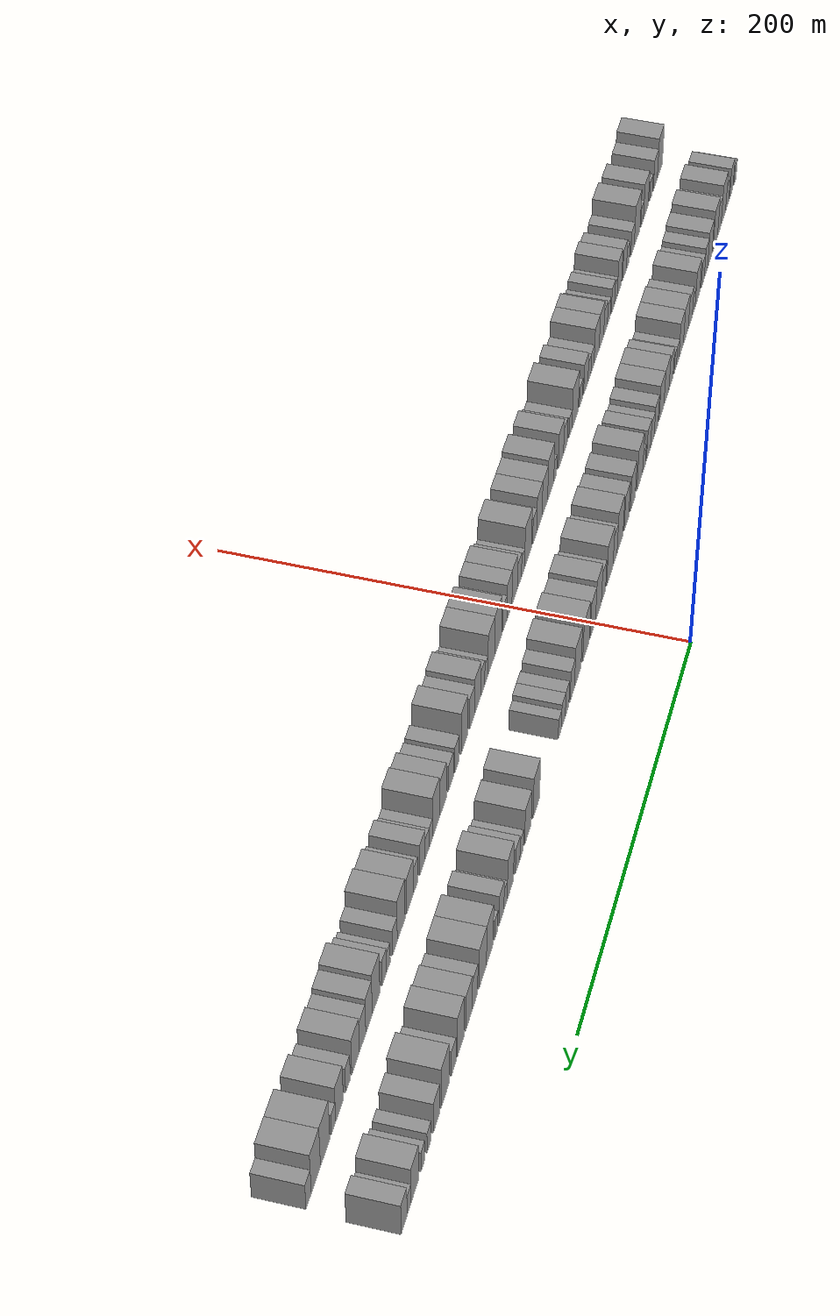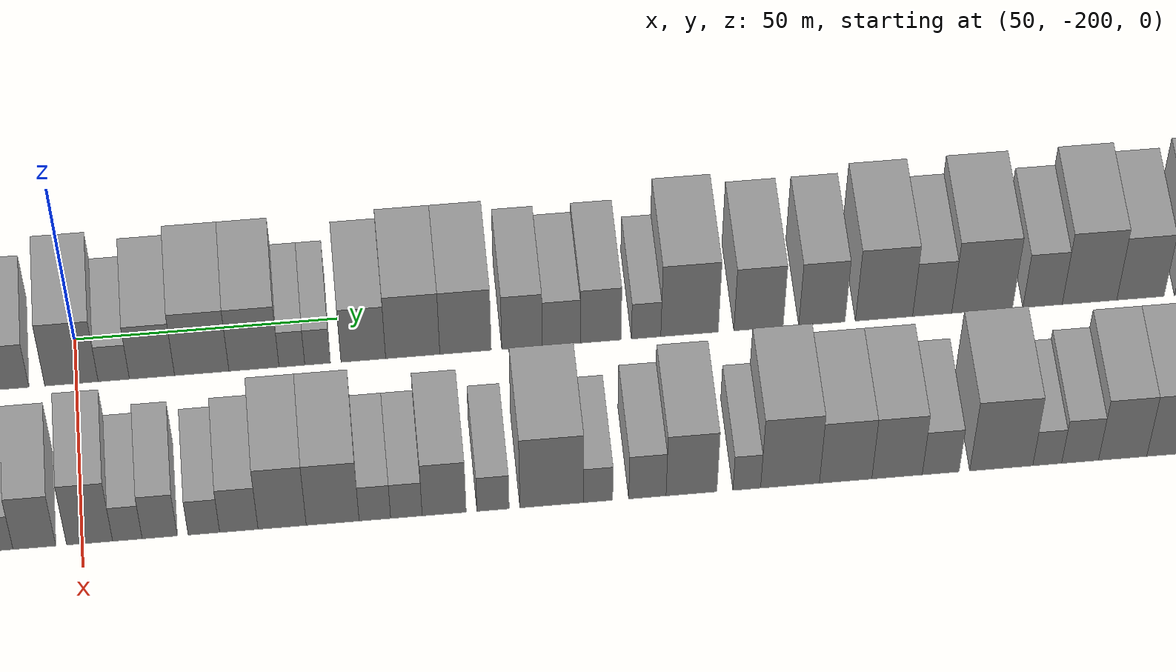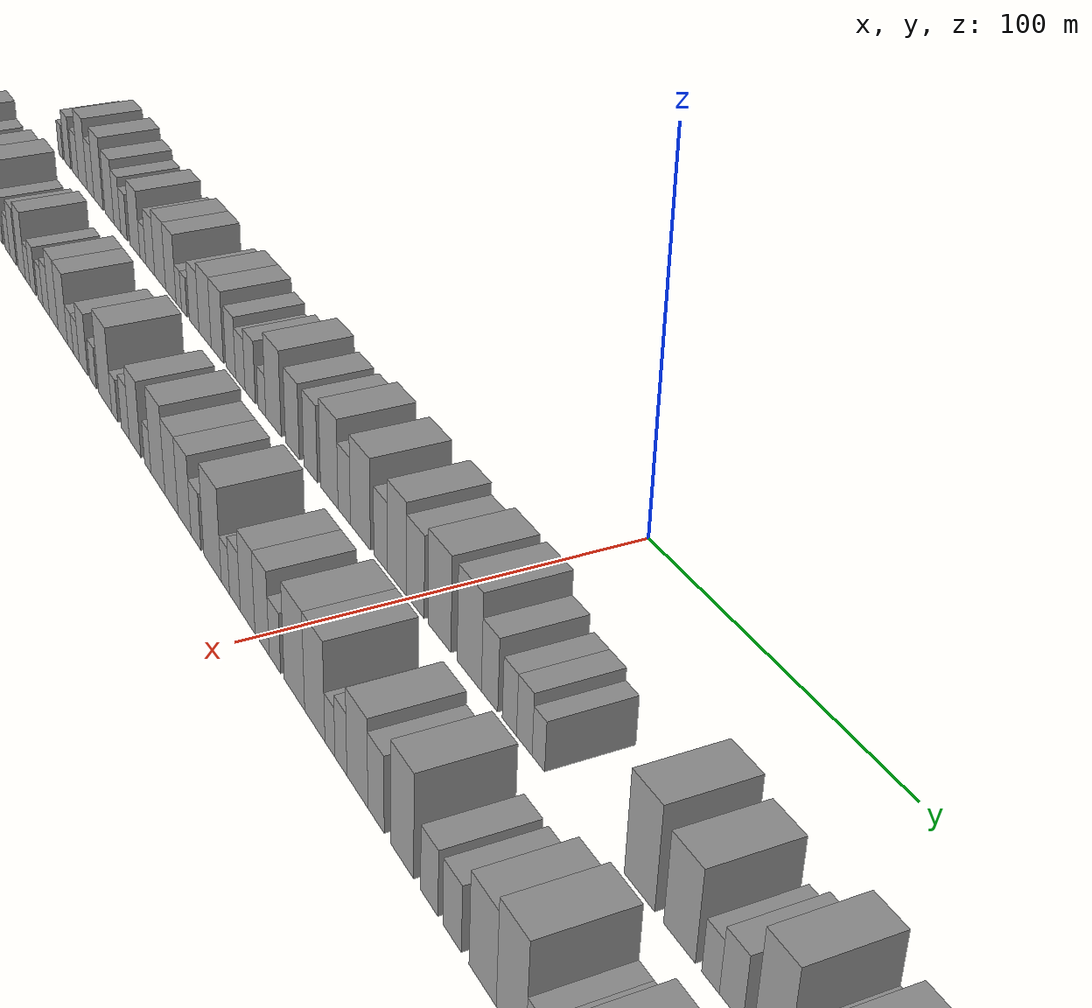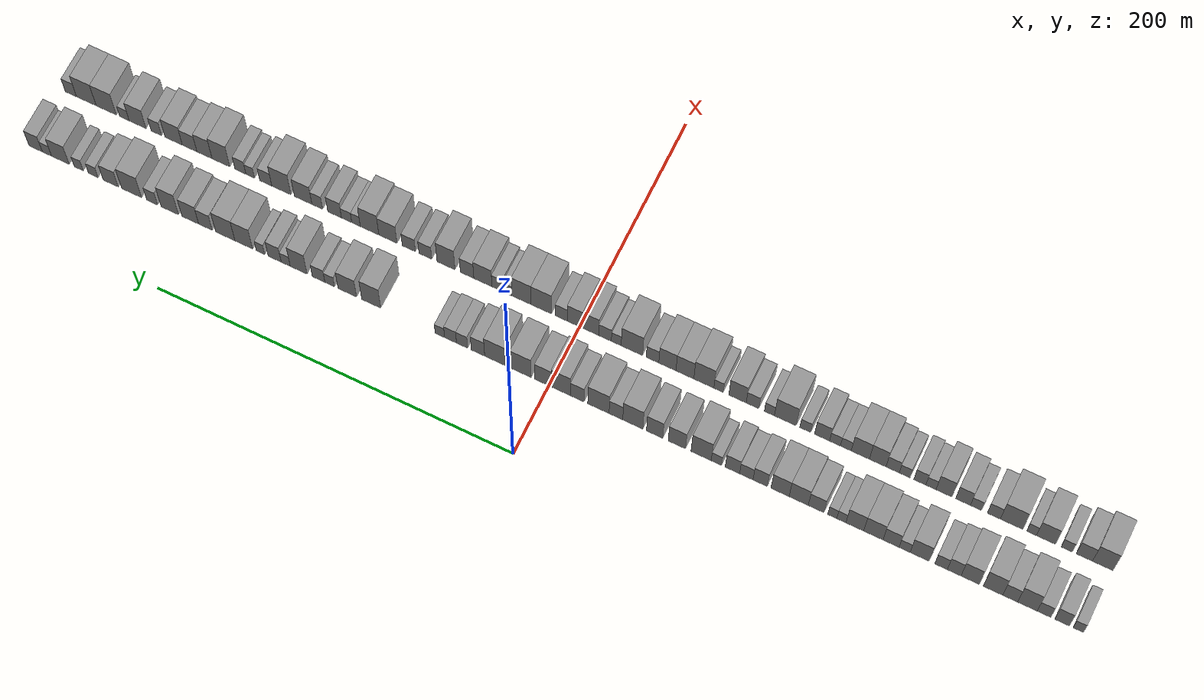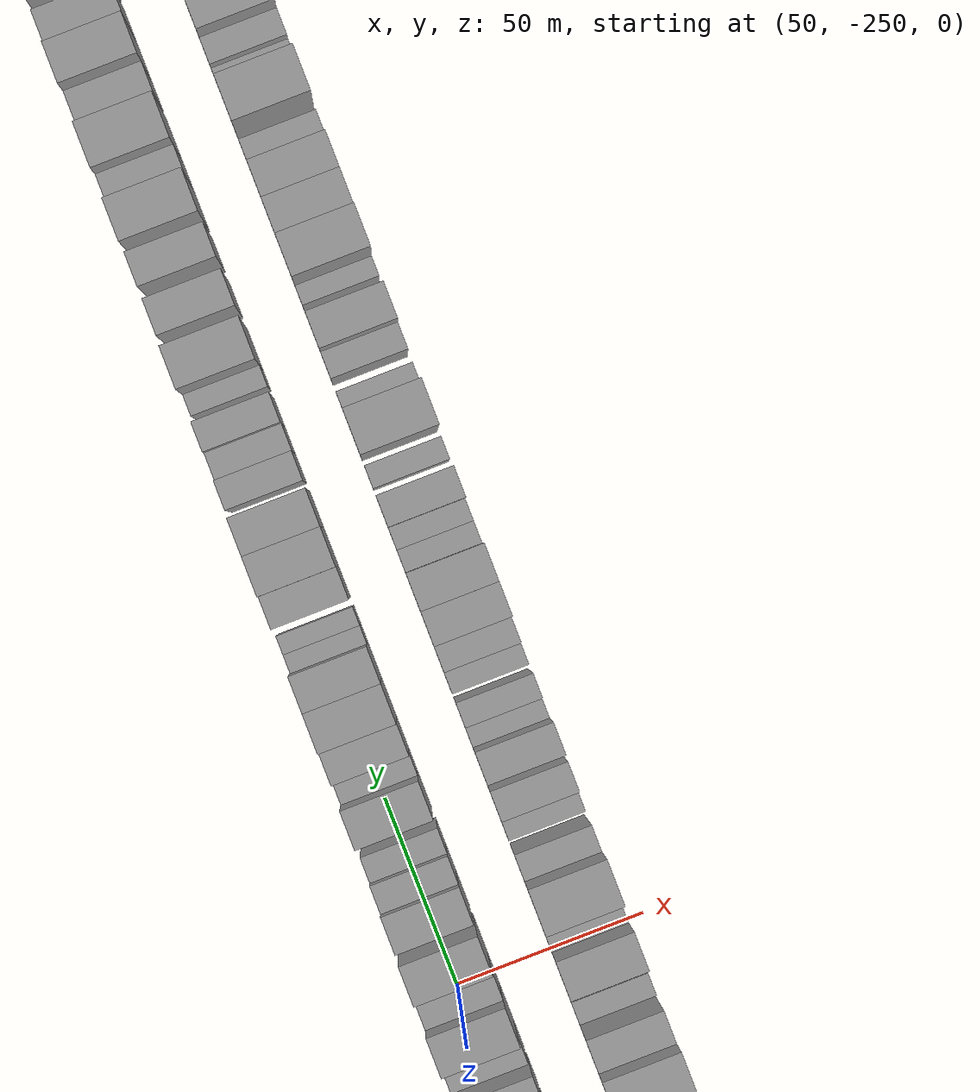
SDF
<sdf version="1.6">
 <world name="default">
  <scene>
   <sky><clouds><speed>12</speed></clouds></sky>
   <ambient>0.4 0.4 0.4 1</ambient>
   <background>0.7 0.7 0.7 1</background>
   <shadows>1</shadows>
  </scene>
  <gravity>0 0 -9.8066</gravity>
  <magnetic_field>6e-06 2.3e-05 -4.2e-05</magnetic_field>
  <physics default="0" name="default_physics" type="ode">
   <ode>
    <solver>
     <type>quick</type>
     <iters>10</iters>
     <sor>1.0</sor>
     <use_dynamic_moi_rescaling>0</use_dynamic_moi_rescaling>
    </solver>
    <constraints>
     <cfm>0</cfm>
     <erp>0.2</erp>
     <contact_max_correcting_vel>100</contact_max_correcting_vel>
     <contact_surface_layer>0.001</contact_surface_layer>
    </constraints>
   </ode>
   <max_step_size>0.004</max_step_size>
   <real_time_factor>1</real_time_factor>
   <real_time_update_rate>250</real_time_update_rate>
  </physics>
  <light name="sun" type="directional">
   <pose>0 0 10 0 0 0</pose>
   <diffuse>0.8 0.8 0.8 1</diffuse>
   <specular>0.2 0.2 0.2 1</specular>
   <attenuation>
    <range>1000</range>
    <constant>0.9</constant>
    <linear>0.01</linear>
    <quadratic>0.001</quadratic>
   </attenuation>
   <direction>-0.5 0.1 -0.9</direction>
  </light>
  <model name="building_1">
   <static>1</static>
   <pose>50.0000 -284.3320 0 0.000000 0.000000 0.000000</pose>
   <link name="link">
    <pose>0 0 6.00 0 0 0</pose>
    <collision name="collision"><geometry><box><size>20.0000 5.3359 12.0000</size></box></geometry></collision>
    <visual name="visual">
     <cast_shadows>0</cast_shadows>
     <geometry><box><size>20.0000 5.3359 12.0000</size></box></geometry>
     <material>
      <script>
       <uri>model://grey_wall/materials/scripts</uri>
       <uri>model://grey_wall/materials/textures</uri>
       <name>vrc/grey_wall</name>
      </script>
     </material>
    </visual>
   </link>
  </model>
  <model name="building_2">
   <static>1</static>
   <pose>50.0000 -275.8561 0 0.000000 0.000000 0.000000</pose>
   <link name="link">
    <pose>0 0 9.00 0 0 0</pose>
    <collision name="collision"><geometry><box><size>20.0000 7.6160 18.0000</size></box></geometry></collision>
    <visual name="visual">
     <cast_shadows>0</cast_shadows>
     <geometry><box><size>20.0000 7.6160 18.0000</size></box></geometry>
     <material>
      <script>
       <uri>model://grey_wall/materials/scripts</uri>
       <uri>model://grey_wall/materials/textures</uri>
       <name>vrc/grey_wall</name>
      </script>
     </material>
    </visual>
   </link>
  </model>
  <model name="building_3">
   <static>1</static>
   <pose>50.0000 -266.4450 0 0.000000 0.000000 0.000000</pose>
   <link name="link">
    <pose>0 0 7.50 0 0 0</pose>
    <collision name="collision"><geometry><box><size>20.0000 7.2062 15.0000</size></box></geometry></collision>
    <visual name="visual">
     <cast_shadows>0</cast_shadows>
     <geometry><box><size>20.0000 7.2062 15.0000</size></box></geometry>
     <material>
      <script>
       <uri>model://grey_wall/materials/scripts</uri>
       <uri>model://grey_wall/materials/textures</uri>
       <name>vrc/grey_wall</name>
      </script>
     </material>
    </visual>
   </link>
  </model>
  <model name="building_4">
   <static>1</static>
   <pose>50.0000 -257.7383 0 0.000000 0.000000 0.000000</pose>
   <link name="link">
    <pose>0 0 12.00 0 0 0</pose>
    <collision name="collision"><geometry><box><size>20.0000 10.2073 24.0000</size></box></geometry></collision>
    <visual name="visual">
     <cast_shadows>0</cast_shadows>
     <geometry><box><size>20.0000 10.2073 24.0000</size></box></geometry>
     <material>
      <script>
       <uri>model://grey_wall/materials/scripts</uri>
       <uri>model://grey_wall/materials/textures</uri>
       <name>vrc/grey_wall</name>
      </script>
     </material>
    </visual>
   </link>
  </model>
  <model name="building_5">
   <static>1</static>
   <pose>50.0000 -248.7134 0 0.000000 0.000000 0.000000</pose>
   <link name="link">
    <pose>0 0 9.00 0 0 0</pose>
    <collision name="collision"><geometry><box><size>20.0000 7.8425 18.0000</size></box></geometry></collision>
    <visual name="visual">
     <cast_shadows>0</cast_shadows>
     <geometry><box><size>20.0000 7.8425 18.0000</size></box></geometry>
     <material>
      <script>
       <uri>model://grey_wall/materials/scripts</uri>
       <uri>model://grey_wall/materials/textures</uri>
       <name>vrc/grey_wall</name>
      </script>
     </material>
    </visual>
   </link>
  </model>
  <model name="building_6">
   <static>1</static>
   <pose>50.0000 -239.6760 0 0.000000 0.000000 0.000000</pose>
   <link name="link">
    <pose>0 0 12.00 0 0 0</pose>
    <collision name="collision"><geometry><box><size>20.0000 10.2323 24.0000</size></box></geometry></collision>
    <visual name="visual">
     <cast_shadows>0</cast_shadows>
     <geometry><box><size>20.0000 10.2323 24.0000</size></box></geometry>
     <material>
      <script>
       <uri>model://grey_wall/materials/scripts</uri>
       <uri>model://grey_wall/materials/textures</uri>
       <name>vrc/grey_wall</name>
      </script>
     </material>
    </visual>
   </link>
  </model>
  <model name="building_7">
   <static>1</static>
   <pose>50.0000 -227.7089 0 0.000000 0.000000 0.000000</pose>
   <link name="link">
    <pose>0 0 10.50 0 0 0</pose>
    <collision name="collision"><geometry><box><size>20.0000 9.7018 21.0000</size></box></geometry></collision>
    <visual name="visual">
     <cast_shadows>0</cast_shadows>
     <geometry><box><size>20.0000 9.7018 21.0000</size></box></geometry>
     <material>
      <script>
       <uri>model://grey_wall/materials/scripts</uri>
       <uri>model://grey_wall/materials/textures</uri>
       <name>vrc/grey_wall</name>
      </script>
     </material>
    </visual>
   </link>
  </model>
  <model name="building_8">
   <static>1</static>
   <pose>50.0000 -219.2189 0 0.000000 0.000000 0.000000</pose>
   <link name="link">
    <pose>0 0 9.00 0 0 0</pose>
    <collision name="collision"><geometry><box><size>20.0000 7.2784 18.0000</size></box></geometry></collision>
    <visual name="visual">
     <cast_shadows>0</cast_shadows>
     <geometry><box><size>20.0000 7.2784 18.0000</size></box></geometry>
     <material>
      <script>
       <uri>model://grey_wall/materials/scripts</uri>
       <uri>model://grey_wall/materials/textures</uri>
       <name>vrc/grey_wall</name>
      </script>
     </material>
    </visual>
   </link>
  </model>
  <model name="building_9">
   <static>1</static>
   <pose>50.0000 -212.2704 0 0.000000 0.000000 0.000000</pose>
   <link name="link">
    <pose>0 0 7.50 0 0 0</pose>
    <collision name="collision"><geometry><box><size>20.0000 6.6184 15.0000</size></box></geometry></collision>
    <visual name="visual">
     <cast_shadows>0</cast_shadows>
     <geometry><box><size>20.0000 6.6184 15.0000</size></box></geometry>
     <material>
      <script>
       <uri>model://grey_wall/materials/scripts</uri>
       <uri>model://grey_wall/materials/textures</uri>
       <name>vrc/grey_wall</name>
      </script>
     </material>
    </visual>
   </link>
  </model>
  <model name="building_10">
   <static>1</static>
   <pose>50.0000 -200.9258 0 0.000000 0.000000 0.000000</pose>
   <link name="link">
    <pose>0 0 10.50 0 0 0</pose>
    <collision name="collision"><geometry><box><size>20.0000 10.0709 21.0000</size></box></geometry></collision>
    <visual name="visual">
     <cast_shadows>0</cast_shadows>
     <geometry><box><size>20.0000 10.0709 21.0000</size></box></geometry>
     <material>
      <script>
       <uri>model://grey_wall/materials/scripts</uri>
       <uri>model://grey_wall/materials/textures</uri>
       <name>vrc/grey_wall</name>
      </script>
     </material>
    </visual>
   </link>
  </model>
  <model name="building_11">
   <static>1</static>
   <pose>50.0000 -192.9457 0 0.000000 0.000000 0.000000</pose>
   <link name="link">
    <pose>0 0 6.00 0 0 0</pose>
    <collision name="collision"><geometry><box><size>20.0000 5.8891 12.0000</size></box></geometry></collision>
    <visual name="visual">
     <cast_shadows>0</cast_shadows>
     <geometry><box><size>20.0000 5.8891 12.0000</size></box></geometry>
     <material>
      <script>
       <uri>model://grey_wall/materials/scripts</uri>
       <uri>model://grey_wall/materials/textures</uri>
       <name>vrc/grey_wall</name>
      </script>
     </material>
    </visual>
   </link>
  </model>
  <model name="building_12">
   <static>1</static>
   <pose>50.0000 -185.7282 0 0.000000 0.000000 0.000000</pose>
   <link name="link">
    <pose>0 0 9.00 0 0 0</pose>
    <collision name="collision"><geometry><box><size>20.0000 8.5458 18.0000</size></box></geometry></collision>
    <visual name="visual">
     <cast_shadows>0</cast_shadows>
     <geometry><box><size>20.0000 8.5458 18.0000</size></box></geometry>
     <material>
      <script>
       <uri>model://grey_wall/materials/scripts</uri>
       <uri>model://grey_wall/materials/textures</uri>
       <name>vrc/grey_wall</name>
      </script>
     </material>
    </visual>
   </link>
  </model>
  <model name="building_13">
   <static>1</static>
   <pose>50.0000 -176.3089 0 0.000000 0.000000 0.000000</pose>
   <link name="link">
    <pose>0 0 10.50 0 0 0</pose>
    <collision name="collision"><geometry><box><size>20.0000 10.2928 21.0000</size></box></geometry></collision>
    <visual name="visual">
     <cast_shadows>0</cast_shadows>
     <geometry><box><size>20.0000 10.2928 21.0000</size></box></geometry>
     <material>
      <script>
       <uri>model://grey_wall/materials/scripts</uri>
       <uri>model://grey_wall/materials/textures</uri>
       <name>vrc/grey_wall</name>
      </script>
     </material>
    </visual>
   </link>
  </model>
  <model name="building_14">
   <static>1</static>
   <pose>50.0000 -166.4119 0 0.000000 0.000000 0.000000</pose>
   <link name="link">
    <pose>0 0 10.50 0 0 0</pose>
    <collision name="collision"><geometry><box><size>20.0000 9.5012 21.0000</size></box></geometry></collision>
    <visual name="visual">
     <cast_shadows>0</cast_shadows>
     <geometry><box><size>20.0000 9.5012 21.0000</size></box></geometry>
     <material>
      <script>
       <uri>model://grey_wall/materials/scripts</uri>
       <uri>model://grey_wall/materials/textures</uri>
       <name>vrc/grey_wall</name>
      </script>
     </material>
    </visual>
   </link>
  </model>
  <model name="building_15">
   <static>1</static>
   <pose>50.0000 -159.2189 0 0.000000 0.000000 0.000000</pose>
   <link name="link">
    <pose>0 0 6.00 0 0 0</pose>
    <collision name="collision"><geometry><box><size>20.0000 4.8848 12.0000</size></box></geometry></collision>
    <visual name="visual">
     <cast_shadows>0</cast_shadows>
     <geometry><box><size>20.0000 4.8848 12.0000</size></box></geometry>
     <material>
      <script>
       <uri>model://grey_wall/materials/scripts</uri>
       <uri>model://grey_wall/materials/textures</uri>
       <name>vrc/grey_wall</name>
      </script>
     </material>
    </visual>
   </link>
  </model>
  <model name="building_16">
   <static>1</static>
   <pose>50.0000 -154.3433 0 0.000000 0.000000 0.000000</pose>
   <link name="link">
    <pose>0 0 6.00 0 0 0</pose>
    <collision name="collision"><geometry><box><size>20.0000 4.8665 12.0000</size></box></geometry></collision>
    <visual name="visual">
     <cast_shadows>0</cast_shadows>
     <geometry><box><size>20.0000 4.8665 12.0000</size></box></geometry>
     <material>
      <script>
       <uri>model://grey_wall/materials/scripts</uri>
       <uri>model://grey_wall/materials/textures</uri>
       <name>vrc/grey_wall</name>
      </script>
     </material>
    </visual>
   </link>
  </model>
  <model name="building_17">
   <static>1</static>
   <pose>50.0000 -145.6713 0 0.000000 0.000000 0.000000</pose>
   <link name="link">
    <pose>0 0 9.00 0 0 0</pose>
    <collision name="collision"><geometry><box><size>20.0000 8.4777 18.0000</size></box></geometry></collision>
    <visual name="visual">
     <cast_shadows>0</cast_shadows>
     <geometry><box><size>20.0000 8.4777 18.0000</size></box></geometry>
     <material>
      <script>
       <uri>model://grey_wall/materials/scripts</uri>
       <uri>model://grey_wall/materials/textures</uri>
       <name>vrc/grey_wall</name>
      </script>
     </material>
    </visual>
   </link>
  </model>
  <model name="building_18">
   <static>1</static>
   <pose>50.0000 -136.2820 0 0.000000 0.000000 0.000000</pose>
   <link name="link">
    <pose>0 0 10.50 0 0 0</pose>
    <collision name="collision"><geometry><box><size>20.0000 10.3009 21.0000</size></box></geometry></collision>
    <visual name="visual">
     <cast_shadows>0</cast_shadows>
     <geometry><box><size>20.0000 10.3009 21.0000</size></box></geometry>
     <material>
      <script>
       <uri>model://grey_wall/materials/scripts</uri>
       <uri>model://grey_wall/materials/textures</uri>
       <name>vrc/grey_wall</name>
      </script>
     </material>
    </visual>
   </link>
  </model>
  <model name="building_19">
   <static>1</static>
   <pose>50.0000 -126.2274 0 0.000000 0.000000 0.000000</pose>
   <link name="link">
    <pose>0 0 10.50 0 0 0</pose>
    <collision name="collision"><geometry><box><size>20.0000 9.8082 21.0000</size></box></geometry></collision>
    <visual name="visual">
     <cast_shadows>0</cast_shadows>
     <geometry><box><size>20.0000 9.8082 21.0000</size></box></geometry>
     <material>
      <script>
       <uri>model://grey_wall/materials/scripts</uri>
       <uri>model://grey_wall/materials/textures</uri>
       <name>vrc/grey_wall</name>
      </script>
     </material>
    </visual>
   </link>
  </model>
  <model name="building_20">
   <static>1</static>
   <pose>50.0000 -115.4698 0 0.000000 0.000000 0.000000</pose>
   <link name="link">
    <pose>0 0 9.00 0 0 0</pose>
    <collision name="collision"><geometry><box><size>20.0000 7.7070 18.0000</size></box></geometry></collision>
    <visual name="visual">
     <cast_shadows>0</cast_shadows>
     <geometry><box><size>20.0000 7.7070 18.0000</size></box></geometry>
     <material>
      <script>
       <uri>model://grey_wall/materials/scripts</uri>
       <uri>model://grey_wall/materials/textures</uri>
       <name>vrc/grey_wall</name>
      </script>
     </material>
    </visual>
   </link>
  </model>
  <model name="building_21">
   <static>1</static>
   <pose>50.0000 -107.9874 0 0.000000 0.000000 0.000000</pose>
   <link name="link">
    <pose>0 0 7.50 0 0 0</pose>
    <collision name="collision"><geometry><box><size>20.0000 7.2578 15.0000</size></box></geometry></collision>
    <visual name="visual">
     <cast_shadows>0</cast_shadows>
     <geometry><box><size>20.0000 7.2578 15.0000</size></box></geometry>
     <material>
      <script>
       <uri>model://grey_wall/materials/scripts</uri>
       <uri>model://grey_wall/materials/textures</uri>
       <name>vrc/grey_wall</name>
      </script>
     </material>
    </visual>
   </link>
  </model>
  <model name="building_22">
   <static>1</static>
   <pose>50.0000 -100.4647 0 0.000000 0.000000 0.000000</pose>
   <link name="link">
    <pose>0 0 9.00 0 0 0</pose>
    <collision name="collision"><geometry><box><size>20.0000 7.7876 18.0000</size></box></geometry></collision>
    <visual name="visual">
     <cast_shadows>0</cast_shadows>
     <geometry><box><size>20.0000 7.7876 18.0000</size></box></geometry>
     <material>
      <script>
       <uri>model://grey_wall/materials/scripts</uri>
       <uri>model://grey_wall/materials/textures</uri>
       <name>vrc/grey_wall</name>
      </script>
     </material>
    </visual>
   </link>
  </model>
  <model name="building_23">
   <static>1</static>
   <pose>50.0000 -91.7634 0 0.000000 0.000000 0.000000</pose>
   <link name="link">
    <pose>0 0 6.00 0 0 0</pose>
    <collision name="collision"><geometry><box><size>20.0000 5.6151 12.0000</size></box></geometry></collision>
    <visual name="visual">
     <cast_shadows>0</cast_shadows>
     <geometry><box><size>20.0000 5.6151 12.0000</size></box></geometry>
     <material>
      <script>
       <uri>model://grey_wall/materials/scripts</uri>
       <uri>model://grey_wall/materials/textures</uri>
       <name>vrc/grey_wall</name>
      </script>
     </material>
    </visual>
   </link>
  </model>
  <model name="building_24">
   <static>1</static>
   <pose>50.0000 -83.4513 0 0.000000 0.000000 0.000000</pose>
   <link name="link">
    <pose>0 0 12.00 0 0 0</pose>
    <collision name="collision"><geometry><box><size>20.0000 11.0090 24.0000</size></box></geometry></collision>
    <visual name="visual">
     <cast_shadows>0</cast_shadows>
     <geometry><box><size>20.0000 11.0090 24.0000</size></box></geometry>
     <material>
      <script>
       <uri>model://grey_wall/materials/scripts</uri>
       <uri>model://grey_wall/materials/textures</uri>
       <name>vrc/grey_wall</name>
      </script>
     </material>
    </visual>
   </link>
  </model>
  <model name="building_25">
   <static>1</static>
   <pose>50.0000 -70.2266 0 0.000000 0.000000 0.000000</pose>
   <link name="link">
    <pose>0 0 10.50 0 0 0</pose>
    <collision name="collision"><geometry><box><size>20.0000 9.4404 21.0000</size></box></geometry></collision>
    <visual name="visual">
     <cast_shadows>0</cast_shadows>
     <geometry><box><size>20.0000 9.4404 21.0000</size></box></geometry>
     <material>
      <script>
       <uri>model://grey_wall/materials/scripts</uri>
       <uri>model://grey_wall/materials/textures</uri>
       <name>vrc/grey_wall</name>
      </script>
     </material>
    </visual>
   </link>
  </model>
  <model name="building_26">
   <static>1</static>
   <pose>50.0000 -58.0610 0 0.000000 0.000000 0.000000</pose>
   <link name="link">
    <pose>0 0 10.50 0 0 0</pose>
    <collision name="collision"><geometry><box><size>20.0000 8.8907 21.0000</size></box></geometry></collision>
    <visual name="visual">
     <cast_shadows>0</cast_shadows>
     <geometry><box><size>20.0000 8.8907 21.0000</size></box></geometry>
     <material>
      <script>
       <uri>model://grey_wall/materials/scripts</uri>
       <uri>model://grey_wall/materials/textures</uri>
       <name>vrc/grey_wall</name>
      </script>
     </material>
    </visual>
   </link>
  </model>
  <model name="building_27">
   <static>1</static>
   <pose>50.0000 -46.1126 0 0.000000 0.000000 0.000000</pose>
   <link name="link">
    <pose>0 0 12.00 0 0 0</pose>
    <collision name="collision"><geometry><box><size>20.0000 11.0061 24.0000</size></box></geometry></collision>
    <visual name="visual">
     <cast_shadows>0</cast_shadows>
     <geometry><box><size>20.0000 11.0061 24.0000</size></box></geometry>
     <material>
      <script>
       <uri>model://grey_wall/materials/scripts</uri>
       <uri>model://grey_wall/materials/textures</uri>
       <name>vrc/grey_wall</name>
      </script>
     </material>
    </visual>
   </link>
  </model>
  <model name="building_28">
   <static>1</static>
   <pose>50.0000 -36.8444 0 0.000000 0.000000 0.000000</pose>
   <link name="link">
    <pose>0 0 9.00 0 0 0</pose>
    <collision name="collision"><geometry><box><size>20.0000 7.5302 18.0000</size></box></geometry></collision>
    <visual name="visual">
     <cast_shadows>0</cast_shadows>
     <geometry><box><size>20.0000 7.5302 18.0000</size></box></geometry>
     <material>
      <script>
       <uri>model://grey_wall/materials/scripts</uri>
       <uri>model://grey_wall/materials/textures</uri>
       <name>vrc/grey_wall</name>
      </script>
     </material>
    </visual>
   </link>
  </model>
  <model name="building_29">
   <static>1</static>
   <pose>50.0000 -27.2090 0 0.000000 0.000000 0.000000</pose>
   <link name="link">
    <pose>0 0 12.00 0 0 0</pose>
    <collision name="collision"><geometry><box><size>20.0000 11.7405 24.0000</size></box></geometry></collision>
    <visual name="visual">
     <cast_shadows>0</cast_shadows>
     <geometry><box><size>20.0000 11.7405 24.0000</size></box></geometry>
     <material>
      <script>
       <uri>model://grey_wall/materials/scripts</uri>
       <uri>model://grey_wall/materials/textures</uri>
       <name>vrc/grey_wall</name>
      </script>
     </material>
    </visual>
   </link>
  </model>
  <model name="building_30">
   <static>1</static>
   <pose>50.0000 -15.5463 0 0.000000 0.000000 0.000000</pose>
   <link name="link">
    <pose>0 0 9.00 0 0 0</pose>
    <collision name="collision"><geometry><box><size>20.0000 7.5850 18.0000</size></box></geometry></collision>
    <visual name="visual">
     <cast_shadows>0</cast_shadows>
     <geometry><box><size>20.0000 7.5850 18.0000</size></box></geometry>
     <material>
      <script>
       <uri>model://grey_wall/materials/scripts</uri>
       <uri>model://grey_wall/materials/textures</uri>
       <name>vrc/grey_wall</name>
      </script>
     </material>
    </visual>
   </link>
  </model>
  <model name="building_31">
   <static>1</static>
   <pose>50.0000 -6.4729 0 0.000000 0.000000 0.000000</pose>
   <link name="link">
    <pose>0 0 12.00 0 0 0</pose>
    <collision name="collision"><geometry><box><size>20.0000 10.5618 24.0000</size></box></geometry></collision>
    <visual name="visual">
     <cast_shadows>0</cast_shadows>
     <geometry><box><size>20.0000 10.5618 24.0000</size></box></geometry>
     <material>
      <script>
       <uri>model://grey_wall/materials/scripts</uri>
       <uri>model://grey_wall/materials/textures</uri>
       <name>vrc/grey_wall</name>
      </script>
     </material>
    </visual>
   </link>
  </model>
  <model name="building_32">
   <static>1</static>
   <pose>50.0000 3.3889 0 0.000000 0.000000 0.000000</pose>
   <link name="link">
    <pose>0 0 10.50 0 0 0</pose>
    <collision name="collision"><geometry><box><size>20.0000 9.1619 21.0000</size></box></geometry></collision>
    <visual name="visual">
     <cast_shadows>0</cast_shadows>
     <geometry><box><size>20.0000 9.1619 21.0000</size></box></geometry>
     <material>
      <script>
       <uri>model://grey_wall/materials/scripts</uri>
       <uri>model://grey_wall/materials/textures</uri>
       <name>vrc/grey_wall</name>
      </script>
     </material>
    </visual>
   </link>
  </model>
  <model name="building_33">
   <static>1</static>
   <pose>50.0000 15.7041 0 0.000000 0.000000 0.000000</pose>
   <link name="link">
    <pose>0 0 12.00 0 0 0</pose>
    <collision name="collision"><geometry><box><size>20.0000 11.4685 24.0000</size></box></geometry></collision>
    <visual name="visual">
     <cast_shadows>0</cast_shadows>
     <geometry><box><size>20.0000 11.4685 24.0000</size></box></geometry>
     <material>
      <script>
       <uri>model://grey_wall/materials/scripts</uri>
       <uri>model://grey_wall/materials/textures</uri>
       <name>vrc/grey_wall</name>
      </script>
     </material>
    </visual>
   </link>
  </model>
  <model name="building_34">
   <static>1</static>
   <pose>50.0000 30.1727 0 0.000000 0.000000 0.000000</pose>
   <link name="link">
    <pose>0 0 12.00 0 0 0</pose>
    <collision name="collision"><geometry><box><size>20.0000 11.4687 24.0000</size></box></geometry></collision>
    <visual name="visual">
     <cast_shadows>0</cast_shadows>
     <geometry><box><size>20.0000 11.4687 24.0000</size></box></geometry>
     <material>
      <script>
       <uri>model://grey_wall/materials/scripts</uri>
       <uri>model://grey_wall/materials/textures</uri>
       <name>vrc/grey_wall</name>
      </script>
     </material>
    </visual>
   </link>
  </model>
  <model name="building_35">
   <static>1</static>
   <pose>50.0000 39.6602 0 0.000000 0.000000 0.000000</pose>
   <link name="link">
    <pose>0 0 9.00 0 0 0</pose>
    <collision name="collision"><geometry><box><size>20.0000 7.5063 18.0000</size></box></geometry></collision>
    <visual name="visual">
     <cast_shadows>0</cast_shadows>
     <geometry><box><size>20.0000 7.5063 18.0000</size></box></geometry>
     <material>
      <script>
       <uri>model://grey_wall/materials/scripts</uri>
       <uri>model://grey_wall/materials/textures</uri>
       <name>vrc/grey_wall</name>
      </script>
     </material>
    </visual>
   </link>
  </model>
  <model name="building_36">
   <static>1</static>
   <pose>50.0000 48.5422 0 0.000000 0.000000 0.000000</pose>
   <link name="link">
    <pose>0 0 7.50 0 0 0</pose>
    <collision name="collision"><geometry><box><size>20.0000 6.2576 15.0000</size></box></geometry></collision>
    <visual name="visual">
     <cast_shadows>0</cast_shadows>
     <geometry><box><size>20.0000 6.2576 15.0000</size></box></geometry>
     <material>
      <script>
       <uri>model://grey_wall/materials/scripts</uri>
       <uri>model://grey_wall/materials/textures</uri>
       <name>vrc/grey_wall</name>
      </script>
     </material>
    </visual>
   </link>
  </model>
  <model name="building_37">
   <static>1</static>
   <pose>50.0000 55.0027 0 0.000000 0.000000 0.000000</pose>
   <link name="link">
    <pose>0 0 7.50 0 0 0</pose>
    <collision name="collision"><geometry><box><size>20.0000 6.6635 15.0000</size></box></geometry></collision>
    <visual name="visual">
     <cast_shadows>0</cast_shadows>
     <geometry><box><size>20.0000 6.6635 15.0000</size></box></geometry>
     <material>
      <script>
       <uri>model://grey_wall/materials/scripts</uri>
       <uri>model://grey_wall/materials/textures</uri>
       <name>vrc/grey_wall</name>
      </script>
     </material>
    </visual>
   </link>
  </model>
  <model name="building_38">
   <static>1</static>
   <pose>50.0000 60.9826 0 0.000000 0.000000 0.000000</pose>
   <link name="link">
    <pose>0 0 6.00 0 0 0</pose>
    <collision name="collision"><geometry><box><size>20.0000 5.2962 12.0000</size></box></geometry></collision>
    <visual name="visual">
     <cast_shadows>0</cast_shadows>
     <geometry><box><size>20.0000 5.2962 12.0000</size></box></geometry>
     <material>
      <script>
       <uri>model://grey_wall/materials/scripts</uri>
       <uri>model://grey_wall/materials/textures</uri>
       <name>vrc/grey_wall</name>
      </script>
     </material>
    </visual>
   </link>
  </model>
  <model name="building_39">
   <static>1</static>
   <pose>50.0000 99.6997 0 0.000000 0.000000 0.000000</pose>
   <link name="link">
    <pose>0 0 12.00 0 0 0</pose>
    <collision name="collision"><geometry><box><size>20.0000 10.7127 24.0000</size></box></geometry></collision>
    <visual name="visual">
     <cast_shadows>0</cast_shadows>
     <geometry><box><size>20.0000 10.7127 24.0000</size></box></geometry>
     <material>
      <script>
       <uri>model://grey_wall/materials/scripts</uri>
       <uri>model://grey_wall/materials/textures</uri>
       <name>vrc/grey_wall</name>
      </script>
     </material>
    </visual>
   </link>
  </model>
  <model name="building_40">
   <static>1</static>
   <pose>50.0000 113.2985 0 0.000000 0.000000 0.000000</pose>
   <link name="link">
    <pose>0 0 10.50 0 0 0</pose>
    <collision name="collision"><geometry><box><size>20.0000 10.4848 21.0000</size></box></geometry></collision>
    <visual name="visual">
     <cast_shadows>0</cast_shadows>
     <geometry><box><size>20.0000 10.4848 21.0000</size></box></geometry>
     <material>
      <script>
       <uri>model://grey_wall/materials/scripts</uri>
       <uri>model://grey_wall/materials/textures</uri>
       <name>vrc/grey_wall</name>
      </script>
     </material>
    </visual>
   </link>
  </model>
  <model name="building_41">
   <static>1</static>
   <pose>50.0000 123.3057 0 0.000000 0.000000 0.000000</pose>
   <link name="link">
    <pose>0 0 6.00 0 0 0</pose>
    <collision name="collision"><geometry><box><size>20.0000 5.5295 12.0000</size></box></geometry></collision>
    <visual name="visual">
     <cast_shadows>0</cast_shadows>
     <geometry><box><size>20.0000 5.5295 12.0000</size></box></geometry>
     <material>
      <script>
       <uri>model://grey_wall/materials/scripts</uri>
       <uri>model://grey_wall/materials/textures</uri>
       <name>vrc/grey_wall</name>
      </script>
     </material>
    </visual>
   </link>
  </model>
  <model name="building_42">
   <static>1</static>
   <pose>50.0000 129.6413 0 0.000000 0.000000 0.000000</pose>
   <link name="link">
    <pose>0 0 7.50 0 0 0</pose>
    <collision name="collision"><geometry><box><size>20.0000 7.1417 15.0000</size></box></geometry></collision>
    <visual name="visual">
     <cast_shadows>0</cast_shadows>
     <geometry><box><size>20.0000 7.1417 15.0000</size></box></geometry>
     <material>
      <script>
       <uri>model://grey_wall/materials/scripts</uri>
       <uri>model://grey_wall/materials/textures</uri>
       <name>vrc/grey_wall</name>
      </script>
     </material>
    </visual>
   </link>
  </model>
  <model name="building_43">
   <static>1</static>
   <pose>50.0000 141.0162 0 0.000000 0.000000 0.000000</pose>
   <link name="link">
    <pose>0 0 12.00 0 0 0</pose>
    <collision name="collision"><geometry><box><size>20.0000 9.6081 24.0000</size></box></geometry></collision>
    <visual name="visual">
     <cast_shadows>0</cast_shadows>
     <geometry><box><size>20.0000 9.6081 24.0000</size></box></geometry>
     <material>
      <script>
       <uri>model://grey_wall/materials/scripts</uri>
       <uri>model://grey_wall/materials/textures</uri>
       <name>vrc/grey_wall</name>
      </script>
     </material>
    </visual>
   </link>
  </model>
  <model name="building_44">
   <static>1</static>
   <pose>50.0000 148.4141 0 0.000000 0.000000 0.000000</pose>
   <link name="link">
    <pose>0 0 6.00 0 0 0</pose>
    <collision name="collision"><geometry><box><size>20.0000 5.1876 12.0000</size></box></geometry></collision>
    <visual name="visual">
     <cast_shadows>0</cast_shadows>
     <geometry><box><size>20.0000 5.1876 12.0000</size></box></geometry>
     <material>
      <script>
       <uri>model://grey_wall/materials/scripts</uri>
       <uri>model://grey_wall/materials/textures</uri>
       <name>vrc/grey_wall</name>
      </script>
     </material>
    </visual>
   </link>
  </model>
  <model name="building_45">
   <static>1</static>
   <pose>50.0000 154.7307 0 0.000000 0.000000 0.000000</pose>
   <link name="link">
    <pose>0 0 9.00 0 0 0</pose>
    <collision name="collision"><geometry><box><size>20.0000 7.4456 18.0000</size></box></geometry></collision>
    <visual name="visual">
     <cast_shadows>0</cast_shadows>
     <geometry><box><size>20.0000 7.4456 18.0000</size></box></geometry>
     <material>
      <script>
       <uri>model://grey_wall/materials/scripts</uri>
       <uri>model://grey_wall/materials/textures</uri>
       <name>vrc/grey_wall</name>
      </script>
     </material>
    </visual>
   </link>
  </model>
  <model name="building_46">
   <static>1</static>
   <pose>50.0000 162.9121 0 0.000000 0.000000 0.000000</pose>
   <link name="link">
    <pose>0 0 6.00 0 0 0</pose>
    <collision name="collision"><geometry><box><size>20.0000 4.9172 12.0000</size></box></geometry></collision>
    <visual name="visual">
     <cast_shadows>0</cast_shadows>
     <geometry><box><size>20.0000 4.9172 12.0000</size></box></geometry>
     <material>
      <script>
       <uri>model://grey_wall/materials/scripts</uri>
       <uri>model://grey_wall/materials/textures</uri>
       <name>vrc/grey_wall</name>
      </script>
     </material>
    </visual>
   </link>
  </model>
  <model name="building_47">
   <static>1</static>
   <pose>50.0000 172.4851 0 0.000000 0.000000 0.000000</pose>
   <link name="link">
    <pose>0 0 12.00 0 0 0</pose>
    <collision name="collision"><geometry><box><size>20.0000 10.2289 24.0000</size></box></geometry></collision>
    <visual name="visual">
     <cast_shadows>0</cast_shadows>
     <geometry><box><size>20.0000 10.2289 24.0000</size></box></geometry>
     <material>
      <script>
       <uri>model://grey_wall/materials/scripts</uri>
       <uri>model://grey_wall/materials/textures</uri>
       <name>vrc/grey_wall</name>
      </script>
     </material>
    </visual>
   </link>
  </model>
  <model name="building_48">
   <static>1</static>
   <pose>50.0000 183.1370 0 0.000000 0.000000 0.000000</pose>
   <link name="link">
    <pose>0 0 12.00 0 0 0</pose>
    <collision name="collision"><geometry><box><size>20.0000 11.0750 24.0000</size></box></geometry></collision>
    <visual name="visual">
     <cast_shadows>0</cast_shadows>
     <geometry><box><size>20.0000 11.0750 24.0000</size></box></geometry>
     <material>
      <script>
       <uri>model://grey_wall/materials/scripts</uri>
       <uri>model://grey_wall/materials/textures</uri>
       <name>vrc/grey_wall</name>
      </script>
     </material>
    </visual>
   </link>
  </model>
  <model name="building_49">
   <static>1</static>
   <pose>50.0000 194.6000 0 0.000000 0.000000 0.000000</pose>
   <link name="link">
    <pose>0 0 9.00 0 0 0</pose>
    <collision name="collision"><geometry><box><size>20.0000 7.8511 18.0000</size></box></geometry></collision>
    <visual name="visual">
     <cast_shadows>0</cast_shadows>
     <geometry><box><size>20.0000 7.8511 18.0000</size></box></geometry>
     <material>
      <script>
       <uri>model://grey_wall/materials/scripts</uri>
       <uri>model://grey_wall/materials/textures</uri>
       <name>vrc/grey_wall</name>
      </script>
     </material>
    </visual>
   </link>
  </model>
  <model name="building_50">
   <static>1</static>
   <pose>50.0000 203.3567 0 0.000000 0.000000 0.000000</pose>
   <link name="link">
    <pose>0 0 10.50 0 0 0</pose>
    <collision name="collision"><geometry><box><size>20.0000 9.6621 21.0000</size></box></geometry></collision>
    <visual name="visual">
     <cast_shadows>0</cast_shadows>
     <geometry><box><size>20.0000 9.6621 21.0000</size></box></geometry>
     <material>
      <script>
       <uri>model://grey_wall/materials/scripts</uri>
       <uri>model://grey_wall/materials/textures</uri>
       <name>vrc/grey_wall</name>
      </script>
     </material>
    </visual>
   </link>
  </model>
  <model name="building_51">
   <static>1</static>
   <pose>50.0000 215.2399 0 0.000000 0.000000 0.000000</pose>
   <link name="link">
    <pose>0 0 12.00 0 0 0</pose>
    <collision name="collision"><geometry><box><size>20.0000 10.1043 24.0000</size></box></geometry></collision>
    <visual name="visual">
     <cast_shadows>0</cast_shadows>
     <geometry><box><size>20.0000 10.1043 24.0000</size></box></geometry>
     <material>
      <script>
       <uri>model://grey_wall/materials/scripts</uri>
       <uri>model://grey_wall/materials/textures</uri>
       <name>vrc/grey_wall</name>
      </script>
     </material>
    </visual>
   </link>
  </model>
  <model name="building_52">
   <static>1</static>
   <pose>50.0000 225.4772 0 0.000000 0.000000 0.000000</pose>
   <link name="link">
    <pose>0 0 7.50 0 0 0</pose>
    <collision name="collision"><geometry><box><size>20.0000 6.3703 15.0000</size></box></geometry></collision>
    <visual name="visual">
     <cast_shadows>0</cast_shadows>
     <geometry><box><size>20.0000 6.3703 15.0000</size></box></geometry>
     <material>
      <script>
       <uri>model://grey_wall/materials/scripts</uri>
       <uri>model://grey_wall/materials/textures</uri>
       <name>vrc/grey_wall</name>
      </script>
     </material>
    </visual>
   </link>
  </model>
  <model name="building_53">
   <static>1</static>
   <pose>50.0000 237.4804 0 0.000000 0.000000 0.000000</pose>
   <link name="link">
    <pose>0 0 12.00 0 0 0</pose>
    <collision name="collision"><geometry><box><size>20.0000 11.6361 24.0000</size></box></geometry></collision>
    <visual name="visual">
     <cast_shadows>0</cast_shadows>
     <geometry><box><size>20.0000 11.6361 24.0000</size></box></geometry>
     <material>
      <script>
       <uri>model://grey_wall/materials/scripts</uri>
       <uri>model://grey_wall/materials/textures</uri>
       <name>vrc/grey_wall</name>
      </script>
     </material>
    </visual>
   </link>
  </model>
  <model name="building_54">
   <static>1</static>
   <pose>50.0000 249.7048 0 0.000000 0.000000 0.000000</pose>
   <link name="link">
    <pose>0 0 9.00 0 0 0</pose>
    <collision name="collision"><geometry><box><size>20.0000 8.8127 18.0000</size></box></geometry></collision>
    <visual name="visual">
     <cast_shadows>0</cast_shadows>
     <geometry><box><size>20.0000 8.8127 18.0000</size></box></geometry>
     <material>
      <script>
       <uri>model://grey_wall/materials/scripts</uri>
       <uri>model://grey_wall/materials/textures</uri>
       <name>vrc/grey_wall</name>
      </script>
     </material>
    </visual>
   </link>
  </model>
  <model name="building_55">
   <static>1</static>
   <pose>50.0000 259.9337 0 0.000000 0.000000 0.000000</pose>
   <link name="link">
    <pose>0 0 6.00 0 0 0</pose>
    <collision name="collision"><geometry><box><size>20.0000 5.6451 12.0000</size></box></geometry></collision>
    <visual name="visual">
     <cast_shadows>0</cast_shadows>
     <geometry><box><size>20.0000 5.6451 12.0000</size></box></geometry>
     <material>
      <script>
       <uri>model://grey_wall/materials/scripts</uri>
       <uri>model://grey_wall/materials/textures</uri>
       <name>vrc/grey_wall</name>
      </script>
     </material>
    </visual>
   </link>
  </model>
  <model name="building_56">
   <static>1</static>
   <pose>50.0000 268.4048 0 0.000000 0.000000 0.000000</pose>
   <link name="link">
    <pose>0 0 6.00 0 0 0</pose>
    <collision name="collision"><geometry><box><size>20.0000 5.2970 12.0000</size></box></geometry></collision>
    <visual name="visual">
     <cast_shadows>0</cast_shadows>
     <geometry><box><size>20.0000 5.2970 12.0000</size></box></geometry>
     <material>
      <script>
       <uri>model://grey_wall/materials/scripts</uri>
       <uri>model://grey_wall/materials/textures</uri>
       <name>vrc/grey_wall</name>
      </script>
     </material>
    </visual>
   </link>
  </model>
  <model name="building_57">
   <static>1</static>
   <pose>50.0000 279.2249 0 0.000000 0.000000 0.000000</pose>
   <link name="link">
    <pose>0 0 10.50 0 0 0</pose>
    <collision name="collision"><geometry><box><size>20.0000 10.3432 21.0000</size></box></geometry></collision>
    <visual name="visual">
     <cast_shadows>0</cast_shadows>
     <geometry><box><size>20.0000 10.3432 21.0000</size></box></geometry>
     <material>
      <script>
       <uri>model://grey_wall/materials/scripts</uri>
       <uri>model://grey_wall/materials/textures</uri>
       <name>vrc/grey_wall</name>
      </script>
     </material>
    </visual>
   </link>
  </model>
  <model name="building_58">
   <static>1</static>
   <pose>50.0000 287.1103 0 0.000000 0.000000 0.000000</pose>
   <link name="link">
    <pose>0 0 6.00 0 0 0</pose>
    <collision name="collision"><geometry><box><size>20.0000 5.4277 12.0000</size></box></geometry></collision>
    <visual name="visual">
     <cast_shadows>0</cast_shadows>
     <geometry><box><size>20.0000 5.4277 12.0000</size></box></geometry>
     <material>
      <script>
       <uri>model://grey_wall/materials/scripts</uri>
       <uri>model://grey_wall/materials/textures</uri>
       <name>vrc/grey_wall</name>
      </script>
     </material>
    </visual>
   </link>
  </model>
  <model name="building_59">
   <static>1</static>
   <pose>50.0000 293.7684 0 0.000000 0.000000 0.000000</pose>
   <link name="link">
    <pose>0 0 9.00 0 0 0</pose>
    <collision name="collision"><geometry><box><size>20.0000 7.8884 18.0000</size></box></geometry></collision>
    <visual name="visual">
     <cast_shadows>0</cast_shadows>
     <geometry><box><size>20.0000 7.8884 18.0000</size></box></geometry>
     <material>
      <script>
       <uri>model://grey_wall/materials/scripts</uri>
       <uri>model://grey_wall/materials/textures</uri>
       <name>vrc/grey_wall</name>
      </script>
     </material>
    </visual>
   </link>
  </model>
  <model name="building_60">
   <static>1</static>
   <pose>85.0000 -282.6183 0 0.000000 0.000000 0.000000</pose>
   <link name="link">
    <pose>0 0 12.00 0 0 0</pose>
    <collision name="collision"><geometry><box><size>20.0000 10.7634 24.0000</size></box></geometry></collision>
    <visual name="visual">
     <cast_shadows>0</cast_shadows>
     <geometry><box><size>20.0000 10.7634 24.0000</size></box></geometry>
     <material>
      <script>
       <uri>model://grey_wall/materials/scripts</uri>
       <uri>model://grey_wall/materials/textures</uri>
       <name>vrc/grey_wall</name>
      </script>
     </material>
    </visual>
   </link>
  </model>
  <model name="building_61">
   <static>1</static>
   <pose>85.0000 -272.9720 0 0.000000 0.000000 0.000000</pose>
   <link name="link">
    <pose>0 0 9.00 0 0 0</pose>
    <collision name="collision"><geometry><box><size>20.0000 8.5294 18.0000</size></box></geometry></collision>
    <visual name="visual">
     <cast_shadows>0</cast_shadows>
     <geometry><box><size>20.0000 8.5294 18.0000</size></box></geometry>
     <material>
      <script>
       <uri>model://grey_wall/materials/scripts</uri>
       <uri>model://grey_wall/materials/textures</uri>
       <name>vrc/grey_wall</name>
      </script>
     </material>
    </visual>
   </link>
  </model>
  <model name="building_62">
   <static>1</static>
   <pose>85.0000 -263.7568 0 0.000000 0.000000 0.000000</pose>
   <link name="link">
    <pose>0 0 6.00 0 0 0</pose>
    <collision name="collision"><geometry><box><size>20.0000 5.9010 12.0000</size></box></geometry></collision>
    <visual name="visual">
     <cast_shadows>0</cast_shadows>
     <geometry><box><size>20.0000 5.9010 12.0000</size></box></geometry>
     <material>
      <script>
       <uri>model://grey_wall/materials/scripts</uri>
       <uri>model://grey_wall/materials/textures</uri>
       <name>vrc/grey_wall</name>
      </script>
     </material>
    </visual>
   </link>
  </model>
  <model name="building_63">
   <static>1</static>
   <pose>85.0000 -252.7707 0 0.000000 0.000000 0.000000</pose>
   <link name="link">
    <pose>0 0 10.50 0 0 0</pose>
    <collision name="collision"><geometry><box><size>20.0000 10.0710 21.0000</size></box></geometry></collision>
    <visual name="visual">
     <cast_shadows>0</cast_shadows>
     <geometry><box><size>20.0000 10.0710 21.0000</size></box></geometry>
     <material>
      <script>
       <uri>model://grey_wall/materials/scripts</uri>
       <uri>model://grey_wall/materials/textures</uri>
       <name>vrc/grey_wall</name>
      </script>
     </material>
    </visual>
   </link>
  </model>
  <model name="building_64">
   <static>1</static>
   <pose>85.0000 -245.1616 0 0.000000 0.000000 0.000000</pose>
   <link name="link">
    <pose>0 0 6.00 0 0 0</pose>
    <collision name="collision"><geometry><box><size>20.0000 5.1472 12.0000</size></box></geometry></collision>
    <visual name="visual">
     <cast_shadows>0</cast_shadows>
     <geometry><box><size>20.0000 5.1472 12.0000</size></box></geometry>
     <material>
      <script>
       <uri>model://grey_wall/materials/scripts</uri>
       <uri>model://grey_wall/materials/textures</uri>
       <name>vrc/grey_wall</name>
      </script>
     </material>
    </visual>
   </link>
  </model>
  <model name="building_65">
   <static>1</static>
   <pose>85.0000 -234.6139 0 0.000000 0.000000 0.000000</pose>
   <link name="link">
    <pose>0 0 12.00 0 0 0</pose>
    <collision name="collision"><geometry><box><size>20.0000 11.9482 24.0000</size></box></geometry></collision>
    <visual name="visual">
     <cast_shadows>0</cast_shadows>
     <geometry><box><size>20.0000 11.9482 24.0000</size></box></geometry>
     <material>
      <script>
       <uri>model://grey_wall/materials/scripts</uri>
       <uri>model://grey_wall/materials/textures</uri>
       <name>vrc/grey_wall</name>
      </script>
     </material>
    </visual>
   </link>
  </model>
  <model name="building_66">
   <static>1</static>
   <pose>85.0000 -225.1788 0 0.000000 0.000000 0.000000</pose>
   <link name="link">
    <pose>0 0 7.50 0 0 0</pose>
    <collision name="collision"><geometry><box><size>20.0000 6.9221 15.0000</size></box></geometry></collision>
    <visual name="visual">
     <cast_shadows>0</cast_shadows>
     <geometry><box><size>20.0000 6.9221 15.0000</size></box></geometry>
     <material>
      <script>
       <uri>model://grey_wall/materials/scripts</uri>
       <uri>model://grey_wall/materials/textures</uri>
       <name>vrc/grey_wall</name>
      </script>
     </material>
    </visual>
   </link>
  </model>
  <model name="building_67">
   <static>1</static>
   <pose>85.0000 -215.7252 0 0.000000 0.000000 0.000000</pose>
   <link name="link">
    <pose>0 0 6.00 0 0 0</pose>
    <collision name="collision"><geometry><box><size>20.0000 5.9850 12.0000</size></box></geometry></collision>
    <visual name="visual">
     <cast_shadows>0</cast_shadows>
     <geometry><box><size>20.0000 5.9850 12.0000</size></box></geometry>
     <material>
      <script>
       <uri>model://grey_wall/materials/scripts</uri>
       <uri>model://grey_wall/materials/textures</uri>
       <name>vrc/grey_wall</name>
      </script>
     </material>
    </visual>
   </link>
  </model>
  <model name="building_68">
   <static>1</static>
   <pose>85.0000 -208.7974 0 0.000000 0.000000 0.000000</pose>
   <link name="link">
    <pose>0 0 9.00 0 0 0</pose>
    <collision name="collision"><geometry><box><size>20.0000 7.8705 18.0000</size></box></geometry></collision>
    <visual name="visual">
     <cast_shadows>0</cast_shadows>
     <geometry><box><size>20.0000 7.8705 18.0000</size></box></geometry>
     <material>
      <script>
       <uri>model://grey_wall/materials/scripts</uri>
       <uri>model://grey_wall/materials/textures</uri>
       <name>vrc/grey_wall</name>
      </script>
     </material>
    </visual>
   </link>
  </model>
  <model name="building_69">
   <static>1</static>
   <pose>85.0000 -198.6296 0 0.000000 0.000000 0.000000</pose>
   <link name="link">
    <pose>0 0 10.50 0 0 0</pose>
    <collision name="collision"><geometry><box><size>20.0000 8.4652 21.0000</size></box></geometry></collision>
    <visual name="visual">
     <cast_shadows>0</cast_shadows>
     <geometry><box><size>20.0000 8.4652 21.0000</size></box></geometry>
     <material>
      <script>
       <uri>model://grey_wall/materials/scripts</uri>
       <uri>model://grey_wall/materials/textures</uri>
       <name>vrc/grey_wall</name>
      </script>
     </material>
    </visual>
   </link>
  </model>
  <model name="building_70">
   <static>1</static>
   <pose>85.0000 -191.6746 0 0.000000 0.000000 0.000000</pose>
   <link name="link">
    <pose>0 0 6.00 0 0 0</pose>
    <collision name="collision"><geometry><box><size>20.0000 5.4448 12.0000</size></box></geometry></collision>
    <visual name="visual">
     <cast_shadows>0</cast_shadows>
     <geometry><box><size>20.0000 5.4448 12.0000</size></box></geometry>
     <material>
      <script>
       <uri>model://grey_wall/materials/scripts</uri>
       <uri>model://grey_wall/materials/textures</uri>
       <name>vrc/grey_wall</name>
      </script>
     </material>
    </visual>
   </link>
  </model>
  <model name="building_71">
   <static>1</static>
   <pose>85.0000 -185.7089 0 0.000000 0.000000 0.000000</pose>
   <link name="link">
    <pose>0 0 7.50 0 0 0</pose>
    <collision name="collision"><geometry><box><size>20.0000 6.4864 15.0000</size></box></geometry></collision>
    <visual name="visual">
     <cast_shadows>0</cast_shadows>
     <geometry><box><size>20.0000 6.4864 15.0000</size></box></geometry>
     <material>
      <script>
       <uri>model://grey_wall/materials/scripts</uri>
       <uri>model://grey_wall/materials/textures</uri>
       <name>vrc/grey_wall</name>
      </script>
     </material>
    </visual>
   </link>
  </model>
  <model name="building_72">
   <static>1</static>
   <pose>85.0000 -177.5558 0 0.000000 0.000000 0.000000</pose>
   <link name="link">
    <pose>0 0 6.00 0 0 0</pose>
    <collision name="collision"><geometry><box><size>20.0000 5.8199 12.0000</size></box></geometry></collision>
    <visual name="visual">
     <cast_shadows>0</cast_shadows>
     <geometry><box><size>20.0000 5.8199 12.0000</size></box></geometry>
     <material>
      <script>
       <uri>model://grey_wall/materials/scripts</uri>
       <uri>model://grey_wall/materials/textures</uri>
       <name>vrc/grey_wall</name>
      </script>
     </material>
    </visual>
   </link>
  </model>
  <model name="building_73">
   <static>1</static>
   <pose>85.0000 -171.0954 0 0.000000 0.000000 0.000000</pose>
   <link name="link">
    <pose>0 0 7.50 0 0 0</pose>
    <collision name="collision"><geometry><box><size>20.0000 7.1008 15.0000</size></box></geometry></collision>
    <visual name="visual">
     <cast_shadows>0</cast_shadows>
     <geometry><box><size>20.0000 7.1008 15.0000</size></box></geometry>
     <material>
      <script>
       <uri>model://grey_wall/materials/scripts</uri>
       <uri>model://grey_wall/materials/textures</uri>
       <name>vrc/grey_wall</name>
      </script>
     </material>
    </visual>
   </link>
  </model>
  <model name="building_74">
   <static>1</static>
   <pose>85.0000 -163.0825 0 0.000000 0.000000 0.000000</pose>
   <link name="link">
    <pose>0 0 10.50 0 0 0</pose>
    <collision name="collision"><geometry><box><size>20.0000 8.9251 21.0000</size></box></geometry></collision>
    <visual name="visual">
     <cast_shadows>0</cast_shadows>
     <geometry><box><size>20.0000 8.9251 21.0000</size></box></geometry>
     <material>
      <script>
       <uri>model://grey_wall/materials/scripts</uri>
       <uri>model://grey_wall/materials/textures</uri>
       <name>vrc/grey_wall</name>
      </script>
     </material>
    </visual>
   </link>
  </model>
  <model name="building_75">
   <static>1</static>
   <pose>85.0000 -153.7238 0 0.000000 0.000000 0.000000</pose>
   <link name="link">
    <pose>0 0 10.50 0 0 0</pose>
    <collision name="collision"><geometry><box><size>20.0000 9.7922 21.0000</size></box></geometry></collision>
    <visual name="visual">
     <cast_shadows>0</cast_shadows>
     <geometry><box><size>20.0000 9.7922 21.0000</size></box></geometry>
     <material>
      <script>
       <uri>model://grey_wall/materials/scripts</uri>
       <uri>model://grey_wall/materials/textures</uri>
       <name>vrc/grey_wall</name>
      </script>
     </material>
    </visual>
   </link>
  </model>
  <model name="building_76">
   <static>1</static>
   <pose>85.0000 -145.9030 0 0.000000 0.000000 0.000000</pose>
   <link name="link">
    <pose>0 0 6.00 0 0 0</pose>
    <collision name="collision"><geometry><box><size>20.0000 5.8493 12.0000</size></box></geometry></collision>
    <visual name="visual">
     <cast_shadows>0</cast_shadows>
     <geometry><box><size>20.0000 5.8493 12.0000</size></box></geometry>
     <material>
      <script>
       <uri>model://grey_wall/materials/scripts</uri>
       <uri>model://grey_wall/materials/textures</uri>
       <name>vrc/grey_wall</name>
      </script>
     </material>
    </visual>
   </link>
  </model>
  <model name="building_77">
   <static>1</static>
   <pose>85.0000 -140.0533 0 0.000000 0.000000 0.000000</pose>
   <link name="link">
    <pose>0 0 6.00 0 0 0</pose>
    <collision name="collision"><geometry><box><size>20.0000 5.8501 12.0000</size></box></geometry></collision>
    <visual name="visual">
     <cast_shadows>0</cast_shadows>
     <geometry><box><size>20.0000 5.8501 12.0000</size></box></geometry>
     <material>
      <script>
       <uri>model://grey_wall/materials/scripts</uri>
       <uri>model://grey_wall/materials/textures</uri>
       <name>vrc/grey_wall</name>
      </script>
     </material>
    </visual>
   </link>
  </model>
  <model name="building_78">
   <static>1</static>
   <pose>85.0000 -133.0357 0 0.000000 0.000000 0.000000</pose>
   <link name="link">
    <pose>0 0 9.00 0 0 0</pose>
    <collision name="collision"><geometry><box><size>20.0000 8.1851 18.0000</size></box></geometry></collision>
    <visual name="visual">
     <cast_shadows>0</cast_shadows>
     <geometry><box><size>20.0000 8.1851 18.0000</size></box></geometry>
     <material>
      <script>
       <uri>model://grey_wall/materials/scripts</uri>
       <uri>model://grey_wall/materials/textures</uri>
       <name>vrc/grey_wall</name>
      </script>
     </material>
    </visual>
   </link>
  </model>
  <model name="building_79">
   <static>1</static>
   <pose>85.0000 -123.9470 0 0.000000 0.000000 0.000000</pose>
   <link name="link">
    <pose>0 0 6.00 0 0 0</pose>
    <collision name="collision"><geometry><box><size>20.0000 5.9923 12.0000</size></box></geometry></collision>
    <visual name="visual">
     <cast_shadows>0</cast_shadows>
     <geometry><box><size>20.0000 5.9923 12.0000</size></box></geometry>
     <material>
      <script>
       <uri>model://grey_wall/materials/scripts</uri>
       <uri>model://grey_wall/materials/textures</uri>
       <name>vrc/grey_wall</name>
      </script>
     </material>
    </visual>
   </link>
  </model>
  <model name="building_80">
   <static>1</static>
   <pose>85.0000 -113.0246 0 0.000000 0.000000 0.000000</pose>
   <link name="link">
    <pose>0 0 12.00 0 0 0</pose>
    <collision name="collision"><geometry><box><size>20.0000 11.8526 24.0000</size></box></geometry></collision>
    <visual name="visual">
     <cast_shadows>0</cast_shadows>
     <geometry><box><size>20.0000 11.8526 24.0000</size></box></geometry>
     <material>
      <script>
       <uri>model://grey_wall/materials/scripts</uri>
       <uri>model://grey_wall/materials/textures</uri>
       <name>vrc/grey_wall</name>
      </script>
     </material>
    </visual>
   </link>
  </model>
  <model name="building_81">
   <static>1</static>
   <pose>85.0000 -104.3825 0 0.000000 0.000000 0.000000</pose>
   <link name="link">
    <pose>0 0 6.00 0 0 0</pose>
    <collision name="collision"><geometry><box><size>20.0000 5.4315 12.0000</size></box></geometry></collision>
    <visual name="visual">
     <cast_shadows>0</cast_shadows>
     <geometry><box><size>20.0000 5.4315 12.0000</size></box></geometry>
     <material>
      <script>
       <uri>model://grey_wall/materials/scripts</uri>
       <uri>model://grey_wall/materials/textures</uri>
       <name>vrc/grey_wall</name>
      </script>
     </material>
    </visual>
   </link>
  </model>
  <model name="building_82">
   <static>1</static>
   <pose>85.0000 -95.1820 0 0.000000 0.000000 0.000000</pose>
   <link name="link">
    <pose>0 0 7.50 0 0 0</pose>
    <collision name="collision"><geometry><box><size>20.0000 6.9696 15.0000</size></box></geometry></collision>
    <visual name="visual">
     <cast_shadows>0</cast_shadows>
     <geometry><box><size>20.0000 6.9696 15.0000</size></box></geometry>
     <material>
      <script>
       <uri>model://grey_wall/materials/scripts</uri>
       <uri>model://grey_wall/materials/textures</uri>
       <name>vrc/grey_wall</name>
      </script>
     </material>
    </visual>
   </link>
  </model>
  <model name="building_83">
   <static>1</static>
   <pose>85.0000 -86.9440 0 0.000000 0.000000 0.000000</pose>
   <link name="link">
    <pose>0 0 10.50 0 0 0</pose>
    <collision name="collision"><geometry><box><size>20.0000 9.5066 21.0000</size></box></geometry></collision>
    <visual name="visual">
     <cast_shadows>0</cast_shadows>
     <geometry><box><size>20.0000 9.5066 21.0000</size></box></geometry>
     <material>
      <script>
       <uri>model://grey_wall/materials/scripts</uri>
       <uri>model://grey_wall/materials/textures</uri>
       <name>vrc/grey_wall</name>
      </script>
     </material>
    </visual>
   </link>
  </model>
  <model name="building_84">
   <static>1</static>
   <pose>85.0000 -76.5993 0 0.000000 0.000000 0.000000</pose>
   <link name="link">
    <pose>0 0 6.00 0 0 0</pose>
    <collision name="collision"><geometry><box><size>20.0000 5.1828 12.0000</size></box></geometry></collision>
    <visual name="visual">
     <cast_shadows>0</cast_shadows>
     <geometry><box><size>20.0000 5.1828 12.0000</size></box></geometry>
     <material>
      <script>
       <uri>model://grey_wall/materials/scripts</uri>
       <uri>model://grey_wall/materials/textures</uri>
       <name>vrc/grey_wall</name>
      </script>
     </material>
    </visual>
   </link>
  </model>
  <model name="building_85">
   <static>1</static>
   <pose>85.0000 -68.5013 0 0.000000 0.000000 0.000000</pose>
   <link name="link">
    <pose>0 0 12.00 0 0 0</pose>
    <collision name="collision"><geometry><box><size>20.0000 11.0131 24.0000</size></box></geometry></collision>
    <visual name="visual">
     <cast_shadows>0</cast_shadows>
     <geometry><box><size>20.0000 11.0131 24.0000</size></box></geometry>
     <material>
      <script>
       <uri>model://grey_wall/materials/scripts</uri>
       <uri>model://grey_wall/materials/textures</uri>
       <name>vrc/grey_wall</name>
      </script>
     </material>
    </visual>
   </link>
  </model>
  <model name="building_86">
   <static>1</static>
   <pose>85.0000 -58.0764 0 0.000000 0.000000 0.000000</pose>
   <link name="link">
    <pose>0 0 10.50 0 0 0</pose>
    <collision name="collision"><geometry><box><size>20.0000 9.8368 21.0000</size></box></geometry></collision>
    <visual name="visual">
     <cast_shadows>0</cast_shadows>
     <geometry><box><size>20.0000 9.8368 21.0000</size></box></geometry>
     <material>
      <script>
       <uri>model://grey_wall/materials/scripts</uri>
       <uri>model://grey_wall/materials/textures</uri>
       <name>vrc/grey_wall</name>
      </script>
     </material>
    </visual>
   </link>
  </model>
  <model name="building_87">
   <static>1</static>
   <pose>85.0000 -48.4231 0 0.000000 0.000000 0.000000</pose>
   <link name="link">
    <pose>0 0 10.50 0 0 0</pose>
    <collision name="collision"><geometry><box><size>20.0000 9.4697 21.0000</size></box></geometry></collision>
    <visual name="visual">
     <cast_shadows>0</cast_shadows>
     <geometry><box><size>20.0000 9.4697 21.0000</size></box></geometry>
     <material>
      <script>
       <uri>model://grey_wall/materials/scripts</uri>
       <uri>model://grey_wall/materials/textures</uri>
       <name>vrc/grey_wall</name>
      </script>
     </material>
    </visual>
   </link>
  </model>
  <model name="building_88">
   <static>1</static>
   <pose>85.0000 -40.2184 0 0.000000 0.000000 0.000000</pose>
   <link name="link">
    <pose>0 0 7.50 0 0 0</pose>
    <collision name="collision"><geometry><box><size>20.0000 6.9398 15.0000</size></box></geometry></collision>
    <visual name="visual">
     <cast_shadows>0</cast_shadows>
     <geometry><box><size>20.0000 6.9398 15.0000</size></box></geometry>
     <material>
      <script>
       <uri>model://grey_wall/materials/scripts</uri>
       <uri>model://grey_wall/materials/textures</uri>
       <name>vrc/grey_wall</name>
      </script>
     </material>
    </visual>
   </link>
  </model>
  <model name="building_89">
   <static>1</static>
   <pose>85.0000 -28.8051 0 0.000000 0.000000 0.000000</pose>
   <link name="link">
    <pose>0 0 12.00 0 0 0</pose>
    <collision name="collision"><geometry><box><size>20.0000 11.8869 24.0000</size></box></geometry></collision>
    <visual name="visual">
     <cast_shadows>0</cast_shadows>
     <geometry><box><size>20.0000 11.8869 24.0000</size></box></geometry>
     <material>
      <script>
       <uri>model://grey_wall/materials/scripts</uri>
       <uri>model://grey_wall/materials/textures</uri>
       <name>vrc/grey_wall</name>
      </script>
     </material>
    </visual>
   </link>
  </model>
  <model name="building_90">
   <static>1</static>
   <pose>85.0000 -20.1417 0 0.000000 0.000000 0.000000</pose>
   <link name="link">
    <pose>0 0 6.00 0 0 0</pose>
    <collision name="collision"><geometry><box><size>20.0000 5.4399 12.0000</size></box></geometry></collision>
    <visual name="visual">
     <cast_shadows>0</cast_shadows>
     <geometry><box><size>20.0000 5.4399 12.0000</size></box></geometry>
     <material>
      <script>
       <uri>model://grey_wall/materials/scripts</uri>
       <uri>model://grey_wall/materials/textures</uri>
       <name>vrc/grey_wall</name>
      </script>
     </material>
    </visual>
   </link>
  </model>
  <model name="building_91">
   <static>1</static>
   <pose>85.0000 -13.9408 0 0.000000 0.000000 0.000000</pose>
   <link name="link">
    <pose>0 0 7.50 0 0 0</pose>
    <collision name="collision"><geometry><box><size>20.0000 6.9619 15.0000</size></box></geometry></collision>
    <visual name="visual">
     <cast_shadows>0</cast_shadows>
     <geometry><box><size>20.0000 6.9619 15.0000</size></box></geometry>
     <material>
      <script>
       <uri>model://grey_wall/materials/scripts</uri>
       <uri>model://grey_wall/materials/textures</uri>
       <name>vrc/grey_wall</name>
      </script>
     </material>
    </visual>
   </link>
  </model>
  <model name="building_92">
   <static>1</static>
   <pose>85.0000 -5.9028 0 0.000000 0.000000 0.000000</pose>
   <link name="link">
    <pose>0 0 10.50 0 0 0</pose>
    <collision name="collision"><geometry><box><size>20.0000 9.1140 21.0000</size></box></geometry></collision>
    <visual name="visual">
     <cast_shadows>0</cast_shadows>
     <geometry><box><size>20.0000 9.1140 21.0000</size></box></geometry>
     <material>
      <script>
       <uri>model://grey_wall/materials/scripts</uri>
       <uri>model://grey_wall/materials/textures</uri>
       <name>vrc/grey_wall</name>
      </script>
     </material>
    </visual>
   </link>
  </model>
  <model name="building_93">
   <static>1</static>
   <pose>85.0000 2.9292 0 0.000000 0.000000 0.000000</pose>
   <link name="link">
    <pose>0 0 10.50 0 0 0</pose>
    <collision name="collision"><geometry><box><size>20.0000 8.5500 21.0000</size></box></geometry></collision>
    <visual name="visual">
     <cast_shadows>0</cast_shadows>
     <geometry><box><size>20.0000 8.5500 21.0000</size></box></geometry>
     <material>
      <script>
       <uri>model://grey_wall/materials/scripts</uri>
       <uri>model://grey_wall/materials/textures</uri>
       <name>vrc/grey_wall</name>
      </script>
     </material>
    </visual>
   </link>
  </model>
  <model name="building_94">
   <static>1</static>
   <pose>85.0000 10.5627 0 0.000000 0.000000 0.000000</pose>
   <link name="link">
    <pose>0 0 7.50 0 0 0</pose>
    <collision name="collision"><geometry><box><size>20.0000 6.7169 15.0000</size></box></geometry></collision>
    <visual name="visual">
     <cast_shadows>0</cast_shadows>
     <geometry><box><size>20.0000 6.7169 15.0000</size></box></geometry>
     <material>
      <script>
       <uri>model://grey_wall/materials/scripts</uri>
       <uri>model://grey_wall/materials/textures</uri>
       <name>vrc/grey_wall</name>
      </script>
     </material>
    </visual>
   </link>
  </model>
  <model name="building_95">
   <static>1</static>
   <pose>85.0000 21.6450 0 0.000000 0.000000 0.000000</pose>
   <link name="link">
    <pose>0 0 12.00 0 0 0</pose>
    <collision name="collision"><geometry><box><size>20.0000 11.4477 24.0000</size></box></geometry></collision>
    <visual name="visual">
     <cast_shadows>0</cast_shadows>
     <geometry><box><size>20.0000 11.4477 24.0000</size></box></geometry>
     <material>
      <script>
       <uri>model://grey_wall/materials/scripts</uri>
       <uri>model://grey_wall/materials/textures</uri>
       <name>vrc/grey_wall</name>
      </script>
     </material>
    </visual>
   </link>
  </model>
  <model name="building_96">
   <static>1</static>
   <pose>85.0000 32.7857 0 0.000000 0.000000 0.000000</pose>
   <link name="link">
    <pose>0 0 12.00 0 0 0</pose>
    <collision name="collision"><geometry><box><size>20.0000 10.8338 24.0000</size></box></geometry></collision>
    <visual name="visual">
     <cast_shadows>0</cast_shadows>
     <geometry><box><size>20.0000 10.8338 24.0000</size></box></geometry>
     <material>
      <script>
       <uri>model://grey_wall/materials/scripts</uri>
       <uri>model://grey_wall/materials/textures</uri>
       <name>vrc/grey_wall</name>
      </script>
     </material>
    </visual>
   </link>
  </model>
  <model name="building_97">
   <static>1</static>
   <pose>85.0000 40.8037 0 0.000000 0.000000 0.000000</pose>
   <link name="link">
    <pose>0 0 6.00 0 0 0</pose>
    <collision name="collision"><geometry><box><size>20.0000 5.2021 12.0000</size></box></geometry></collision>
    <visual name="visual">
     <cast_shadows>0</cast_shadows>
     <geometry><box><size>20.0000 5.2021 12.0000</size></box></geometry>
     <material>
      <script>
       <uri>model://grey_wall/materials/scripts</uri>
       <uri>model://grey_wall/materials/textures</uri>
       <name>vrc/grey_wall</name>
      </script>
     </material>
    </visual>
   </link>
  </model>
  <model name="building_98">
   <static>1</static>
   <pose>85.0000 46.4059 0 0.000000 0.000000 0.000000</pose>
   <link name="link">
    <pose>0 0 7.50 0 0 0</pose>
    <collision name="collision"><geometry><box><size>20.0000 6.0024 15.0000</size></box></geometry></collision>
    <visual name="visual">
     <cast_shadows>0</cast_shadows>
     <geometry><box><size>20.0000 6.0024 15.0000</size></box></geometry>
     <material>
      <script>
       <uri>model://grey_wall/materials/scripts</uri>
       <uri>model://grey_wall/materials/textures</uri>
       <name>vrc/grey_wall</name>
      </script>
     </material>
    </visual>
   </link>
  </model>
  <model name="building_99">
   <static>1</static>
   <pose>85.0000 54.5249 0 0.000000 0.000000 0.000000</pose>
   <link name="link">
    <pose>0 0 10.50 0 0 0</pose>
    <collision name="collision"><geometry><box><size>20.0000 10.2356 21.0000</size></box></geometry></collision>
    <visual name="visual">
     <cast_shadows>0</cast_shadows>
     <geometry><box><size>20.0000 10.2356 21.0000</size></box></geometry>
     <material>
      <script>
       <uri>model://grey_wall/materials/scripts</uri>
       <uri>model://grey_wall/materials/textures</uri>
       <name>vrc/grey_wall</name>
      </script>
     </material>
    </visual>
   </link>
  </model>
  <model name="building_100">
   <static>1</static>
   <pose>85.0000 63.4577 0 0.000000 0.000000 0.000000</pose>
   <link name="link">
    <pose>0 0 9.00 0 0 0</pose>
    <collision name="collision"><geometry><box><size>20.0000 7.6299 18.0000</size></box></geometry></collision>
    <visual name="visual">
     <cast_shadows>0</cast_shadows>
     <geometry><box><size>20.0000 7.6299 18.0000</size></box></geometry>
     <material>
      <script>
       <uri>model://grey_wall/materials/scripts</uri>
       <uri>model://grey_wall/materials/textures</uri>
       <name>vrc/grey_wall</name>
      </script>
     </material>
    </visual>
   </link>
  </model>
  <model name="building_101">
   <static>1</static>
   <pose>85.0000 75.3697 0 0.000000 0.000000 0.000000</pose>
   <link name="link">
    <pose>0 0 12.00 0 0 0</pose>
    <collision name="collision"><geometry><box><size>20.0000 10.1941 24.0000</size></box></geometry></collision>
    <visual name="visual">
     <cast_shadows>0</cast_shadows>
     <geometry><box><size>20.0000 10.1941 24.0000</size></box></geometry>
     <material>
      <script>
       <uri>model://grey_wall/materials/scripts</uri>
       <uri>model://grey_wall/materials/textures</uri>
       <name>vrc/grey_wall</name>
      </script>
     </material>
    </visual>
   </link>
  </model>
  <model name="building_102">
   <static>1</static>
   <pose>85.0000 87.1028 0 0.000000 0.000000 0.000000</pose>
   <link name="link">
    <pose>0 0 7.50 0 0 0</pose>
    <collision name="collision"><geometry><box><size>20.0000 7.2722 15.0000</size></box></geometry></collision>
    <visual name="visual">
     <cast_shadows>0</cast_shadows>
     <geometry><box><size>20.0000 7.2722 15.0000</size></box></geometry>
     <material>
      <script>
       <uri>model://grey_wall/materials/scripts</uri>
       <uri>model://grey_wall/materials/textures</uri>
       <name>vrc/grey_wall</name>
      </script>
     </material>
    </visual>
   </link>
  </model>
  <model name="building_103">
   <static>1</static>
   <pose>85.0000 96.4759 0 0.000000 0.000000 0.000000</pose>
   <link name="link">
    <pose>0 0 7.50 0 0 0</pose>
    <collision name="collision"><geometry><box><size>20.0000 7.4739 15.0000</size></box></geometry></collision>
    <visual name="visual">
     <cast_shadows>0</cast_shadows>
     <geometry><box><size>20.0000 7.4739 15.0000</size></box></geometry>
     <material>
      <script>
       <uri>model://grey_wall/materials/scripts</uri>
       <uri>model://grey_wall/materials/textures</uri>
       <name>vrc/grey_wall</name>
      </script>
     </material>
    </visual>
   </link>
  </model>
  <model name="building_104">
   <static>1</static>
   <pose>85.0000 108.3923 0 0.000000 0.000000 0.000000</pose>
   <link name="link">
    <pose>0 0 10.50 0 0 0</pose>
    <collision name="collision"><geometry><box><size>20.0000 10.3588 21.0000</size></box></geometry></collision>
    <visual name="visual">
     <cast_shadows>0</cast_shadows>
     <geometry><box><size>20.0000 10.3588 21.0000</size></box></geometry>
     <material>
      <script>
       <uri>model://grey_wall/materials/scripts</uri>
       <uri>model://grey_wall/materials/textures</uri>
       <name>vrc/grey_wall</name>
      </script>
     </material>
    </visual>
   </link>
  </model>
  <model name="building_105">
   <static>1</static>
   <pose>85.0000 118.8786 0 0.000000 0.000000 0.000000</pose>
   <link name="link">
    <pose>0 0 12.00 0 0 0</pose>
    <collision name="collision"><geometry><box><size>20.0000 10.6140 24.0000</size></box></geometry></collision>
    <visual name="visual">
     <cast_shadows>0</cast_shadows>
     <geometry><box><size>20.0000 10.6140 24.0000</size></box></geometry>
     <material>
      <script>
       <uri>model://grey_wall/materials/scripts</uri>
       <uri>model://grey_wall/materials/textures</uri>
       <name>vrc/grey_wall</name>
      </script>
     </material>
    </visual>
   </link>
  </model>
  <model name="building_106">
   <static>1</static>
   <pose>85.0000 126.6306 0 0.000000 0.000000 0.000000</pose>
   <link name="link">
    <pose>0 0 6.00 0 0 0</pose>
    <collision name="collision"><geometry><box><size>20.0000 4.8900 12.0000</size></box></geometry></collision>
    <visual name="visual">
     <cast_shadows>0</cast_shadows>
     <geometry><box><size>20.0000 4.8900 12.0000</size></box></geometry>
     <material>
      <script>
       <uri>model://grey_wall/materials/scripts</uri>
       <uri>model://grey_wall/materials/textures</uri>
       <name>vrc/grey_wall</name>
      </script>
     </material>
    </visual>
   </link>
  </model>
  <model name="building_107">
   <static>1</static>
   <pose>85.0000 132.0474 0 0.000000 0.000000 0.000000</pose>
   <link name="link">
    <pose>0 0 6.00 0 0 0</pose>
    <collision name="collision"><geometry><box><size>20.0000 5.9436 12.0000</size></box></geometry></collision>
    <visual name="visual">
     <cast_shadows>0</cast_shadows>
     <geometry><box><size>20.0000 5.9436 12.0000</size></box></geometry>
     <material>
      <script>
       <uri>model://grey_wall/materials/scripts</uri>
       <uri>model://grey_wall/materials/textures</uri>
       <name>vrc/grey_wall</name>
      </script>
     </material>
    </visual>
   </link>
  </model>
  <model name="building_108">
   <static>1</static>
   <pose>85.0000 138.9345 0 0.000000 0.000000 0.000000</pose>
   <link name="link">
    <pose>0 0 9.00 0 0 0</pose>
    <collision name="collision"><geometry><box><size>20.0000 7.8307 18.0000</size></box></geometry></collision>
    <visual name="visual">
     <cast_shadows>0</cast_shadows>
     <geometry><box><size>20.0000 7.8307 18.0000</size></box></geometry>
     <material>
      <script>
       <uri>model://grey_wall/materials/scripts</uri>
       <uri>model://grey_wall/materials/textures</uri>
       <name>vrc/grey_wall</name>
      </script>
     </material>
    </visual>
   </link>
  </model>
  <model name="building_109">
   <static>1</static>
   <pose>85.0000 148.9403 0 0.000000 0.000000 0.000000</pose>
   <link name="link">
    <pose>0 0 7.50 0 0 0</pose>
    <collision name="collision"><geometry><box><size>20.0000 6.1810 15.0000</size></box></geometry></collision>
    <visual name="visual">
     <cast_shadows>0</cast_shadows>
     <geometry><box><size>20.0000 6.1810 15.0000</size></box></geometry>
     <material>
      <script>
       <uri>model://grey_wall/materials/scripts</uri>
       <uri>model://grey_wall/materials/textures</uri>
       <name>vrc/grey_wall</name>
      </script>
     </material>
    </visual>
   </link>
  </model>
  <model name="building_110">
   <static>1</static>
   <pose>85.0000 157.0736 0 0.000000 0.000000 0.000000</pose>
   <link name="link">
    <pose>0 0 10.50 0 0 0</pose>
    <collision name="collision"><geometry><box><size>20.0000 10.0856 21.0000</size></box></geometry></collision>
    <visual name="visual">
     <cast_shadows>0</cast_shadows>
     <geometry><box><size>20.0000 10.0856 21.0000</size></box></geometry>
     <material>
      <script>
       <uri>model://grey_wall/materials/scripts</uri>
       <uri>model://grey_wall/materials/textures</uri>
       <name>vrc/grey_wall</name>
      </script>
     </material>
    </visual>
   </link>
  </model>
  <model name="building_111">
   <static>1</static>
   <pose>85.0000 169.6368 0 0.000000 0.000000 0.000000</pose>
   <link name="link">
    <pose>0 0 12.00 0 0 0</pose>
    <collision name="collision"><geometry><box><size>20.0000 11.0409 24.0000</size></box></geometry></collision>
    <visual name="visual">
     <cast_shadows>0</cast_shadows>
     <geometry><box><size>20.0000 11.0409 24.0000</size></box></geometry>
     <material>
      <script>
       <uri>model://grey_wall/materials/scripts</uri>
       <uri>model://grey_wall/materials/textures</uri>
       <name>vrc/grey_wall</name>
      </script>
     </material>
    </visual>
   </link>
  </model>
  <model name="building_112">
   <static>1</static>
   <pose>85.0000 178.6583 0 0.000000 0.000000 0.000000</pose>
   <link name="link">
    <pose>0 0 7.50 0 0 0</pose>
    <collision name="collision"><geometry><box><size>20.0000 7.0020 15.0000</size></box></geometry></collision>
    <visual name="visual">
     <cast_shadows>0</cast_shadows>
     <geometry><box><size>20.0000 7.0020 15.0000</size></box></geometry>
     <material>
      <script>
       <uri>model://grey_wall/materials/scripts</uri>
       <uri>model://grey_wall/materials/textures</uri>
       <name>vrc/grey_wall</name>
      </script>
     </material>
    </visual>
   </link>
  </model>
  <model name="building_113">
   <static>1</static>
   <pose>85.0000 187.6630 0 0.000000 0.000000 0.000000</pose>
   <link name="link">
    <pose>0 0 6.00 0 0 0</pose>
    <collision name="collision"><geometry><box><size>20.0000 5.0075 12.0000</size></box></geometry></collision>
    <visual name="visual">
     <cast_shadows>0</cast_shadows>
     <geometry><box><size>20.0000 5.0075 12.0000</size></box></geometry>
     <material>
      <script>
       <uri>model://grey_wall/materials/scripts</uri>
       <uri>model://grey_wall/materials/textures</uri>
       <name>vrc/grey_wall</name>
      </script>
     </material>
    </visual>
   </link>
  </model>
  <model name="building_114">
   <static>1</static>
   <pose>85.0000 193.3498 0 0.000000 0.000000 0.000000</pose>
   <link name="link">
    <pose>0 0 7.50 0 0 0</pose>
    <collision name="collision"><geometry><box><size>20.0000 6.3661 15.0000</size></box></geometry></collision>
    <visual name="visual">
     <cast_shadows>0</cast_shadows>
     <geometry><box><size>20.0000 6.3661 15.0000</size></box></geometry>
     <material>
      <script>
       <uri>model://grey_wall/materials/scripts</uri>
       <uri>model://grey_wall/materials/textures</uri>
       <name>vrc/grey_wall</name>
      </script>
     </material>
    </visual>
   </link>
  </model>
  <model name="building_115">
   <static>1</static>
   <pose>85.0000 204.7141 0 0.000000 0.000000 0.000000</pose>
   <link name="link">
    <pose>0 0 12.00 0 0 0</pose>
    <collision name="collision"><geometry><box><size>20.0000 10.3624 24.0000</size></box></geometry></collision>
    <visual name="visual">
     <cast_shadows>0</cast_shadows>
     <geometry><box><size>20.0000 10.3624 24.0000</size></box></geometry>
     <material>
      <script>
       <uri>model://grey_wall/materials/scripts</uri>
       <uri>model://grey_wall/materials/textures</uri>
       <name>vrc/grey_wall</name>
      </script>
     </material>
    </visual>
   </link>
  </model>
  <model name="building_116">
   <static>1</static>
   <pose>85.0000 214.3122 0 0.000000 0.000000 0.000000</pose>
   <link name="link">
    <pose>0 0 10.50 0 0 0</pose>
    <collision name="collision"><geometry><box><size>20.0000 8.8339 21.0000</size></box></geometry></collision>
    <visual name="visual">
     <cast_shadows>0</cast_shadows>
     <geometry><box><size>20.0000 8.8339 21.0000</size></box></geometry>
     <material>
      <script>
       <uri>model://grey_wall/materials/scripts</uri>
       <uri>model://grey_wall/materials/textures</uri>
       <name>vrc/grey_wall</name>
      </script>
     </material>
    </visual>
   </link>
  </model>
  <model name="building_117">
   <static>1</static>
   <pose>85.0000 222.9933 0 0.000000 0.000000 0.000000</pose>
   <link name="link">
    <pose>0 0 9.00 0 0 0</pose>
    <collision name="collision"><geometry><box><size>20.0000 8.5284 18.0000</size></box></geometry></collision>
    <visual name="visual">
     <cast_shadows>0</cast_shadows>
     <geometry><box><size>20.0000 8.5284 18.0000</size></box></geometry>
     <material>
      <script>
       <uri>model://grey_wall/materials/scripts</uri>
       <uri>model://grey_wall/materials/textures</uri>
       <name>vrc/grey_wall</name>
      </script>
     </material>
    </visual>
   </link>
  </model>
  <model name="building_118">
   <static>1</static>
   <pose>85.0000 232.3444 0 0.000000 0.000000 0.000000</pose>
   <link name="link">
    <pose>0 0 10.50 0 0 0</pose>
    <collision name="collision"><geometry><box><size>20.0000 10.1737 21.0000</size></box></geometry></collision>
    <visual name="visual">
     <cast_shadows>0</cast_shadows>
     <geometry><box><size>20.0000 10.1737 21.0000</size></box></geometry>
     <material>
      <script>
       <uri>model://grey_wall/materials/scripts</uri>
       <uri>model://grey_wall/materials/textures</uri>
       <name>vrc/grey_wall</name>
      </script>
     </material>
    </visual>
   </link>
  </model>
  <model name="building_119">
   <static>1</static>
   <pose>85.0000 242.5098 0 0.000000 0.000000 0.000000</pose>
   <link name="link">
    <pose>0 0 7.50 0 0 0</pose>
    <collision name="collision"><geometry><box><size>20.0000 6.1571 15.0000</size></box></geometry></collision>
    <visual name="visual">
     <cast_shadows>0</cast_shadows>
     <geometry><box><size>20.0000 6.1571 15.0000</size></box></geometry>
     <material>
      <script>
       <uri>model://grey_wall/materials/scripts</uri>
       <uri>model://grey_wall/materials/textures</uri>
       <name>vrc/grey_wall</name>
      </script>
     </material>
    </visual>
   </link>
  </model>
  <model name="building_120">
   <static>1</static>
   <pose>85.0000 253.5652 0 0.000000 0.000000 0.000000</pose>
   <link name="link">
    <pose>0 0 10.50 0 0 0</pose>
    <collision name="collision"><geometry><box><size>20.0000 9.9537 21.0000</size></box></geometry></collision>
    <visual name="visual">
     <cast_shadows>0</cast_shadows>
     <geometry><box><size>20.0000 9.9537 21.0000</size></box></geometry>
     <material>
      <script>
       <uri>model://grey_wall/materials/scripts</uri>
       <uri>model://grey_wall/materials/textures</uri>
       <name>vrc/grey_wall</name>
      </script>
     </material>
    </visual>
   </link>
  </model>
  <model name="building_121">
   <static>1</static>
   <pose>85.0000 261.3185 0 0.000000 0.000000 0.000000</pose>
   <link name="link">
    <pose>0 0 6.00 0 0 0</pose>
    <collision name="collision"><geometry><box><size>20.0000 5.5530 12.0000</size></box></geometry></collision>
    <visual name="visual">
     <cast_shadows>0</cast_shadows>
     <geometry><box><size>20.0000 5.5530 12.0000</size></box></geometry>
     <material>
      <script>
       <uri>model://grey_wall/materials/scripts</uri>
       <uri>model://grey_wall/materials/textures</uri>
       <name>vrc/grey_wall</name>
      </script>
     </material>
    </visual>
   </link>
  </model>
  <model name="building_122">
   <static>1</static>
   <pose>85.0000 272.0554 0 0.000000 0.000000 0.000000</pose>
   <link name="link">
    <pose>0 0 12.00 0 0 0</pose>
    <collision name="collision"><geometry><box><size>20.0000 11.9208 24.0000</size></box></geometry></collision>
    <visual name="visual">
     <cast_shadows>0</cast_shadows>
     <geometry><box><size>20.0000 11.9208 24.0000</size></box></geometry>
     <material>
      <script>
       <uri>model://grey_wall/materials/scripts</uri>
       <uri>model://grey_wall/materials/textures</uri>
       <name>vrc/grey_wall</name>
      </script>
     </material>
    </visual>
   </link>
  </model>
  <model name="building_123">
   <static>1</static>
   <pose>85.0000 283.8300 0 0.000000 0.000000 0.000000</pose>
   <link name="link">
    <pose>0 0 12.00 0 0 0</pose>
    <collision name="collision"><geometry><box><size>20.0000 11.6283 24.0000</size></box></geometry></collision>
    <visual name="visual">
     <cast_shadows>0</cast_shadows>
     <geometry><box><size>20.0000 11.6283 24.0000</size></box></geometry>
     <material>
      <script>
       <uri>model://grey_wall/materials/scripts</uri>
       <uri>model://grey_wall/materials/textures</uri>
       <name>vrc/grey_wall</name>
      </script>
     </material>
    </visual>
   </link>
  </model>
  <model name="building_124">
   <static>1</static>
   <pose>85.0000 292.9630 0 0.000000 0.000000 0.000000</pose>
   <link name="link">
    <pose>0 0 7.50 0 0 0</pose>
    <collision name="collision"><geometry><box><size>20.0000 6.6377 15.0000</size></box></geometry></collision>
    <visual name="visual">
     <cast_shadows>0</cast_shadows>
     <geometry><box><size>20.0000 6.6377 15.0000</size></box></geometry>
     <material>
      <script>
       <uri>model://grey_wall/materials/scripts</uri>
       <uri>model://grey_wall/materials/textures</uri>
       <name>vrc/grey_wall</name>
      </script>
     </material>
    </visual>
   </link>
  </model>
 </world>
</sdf>
